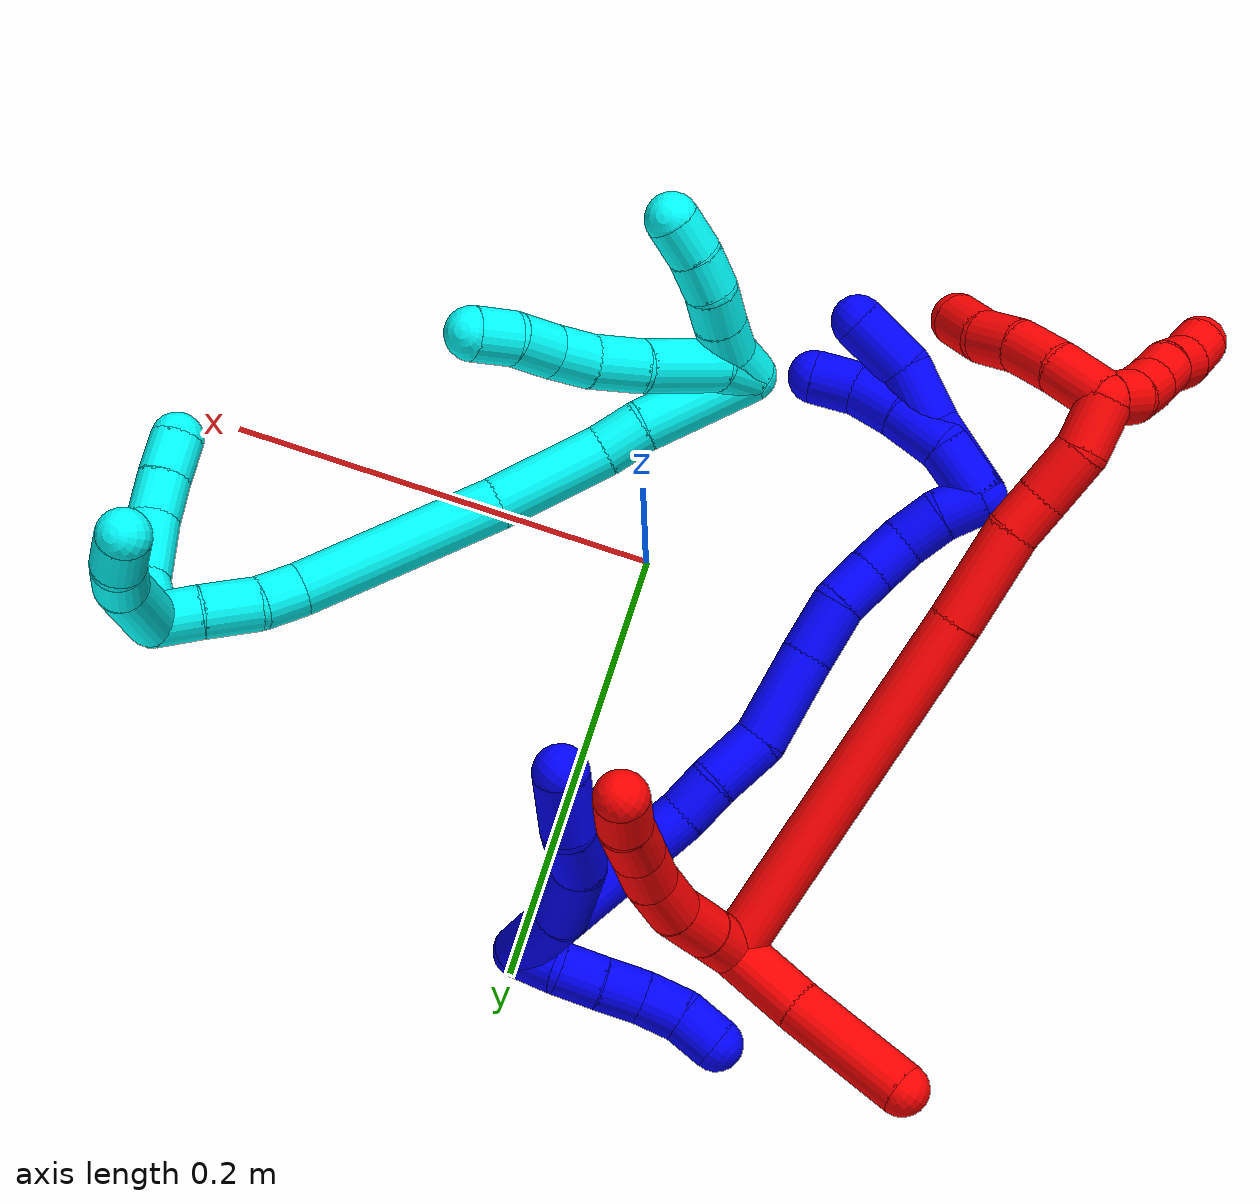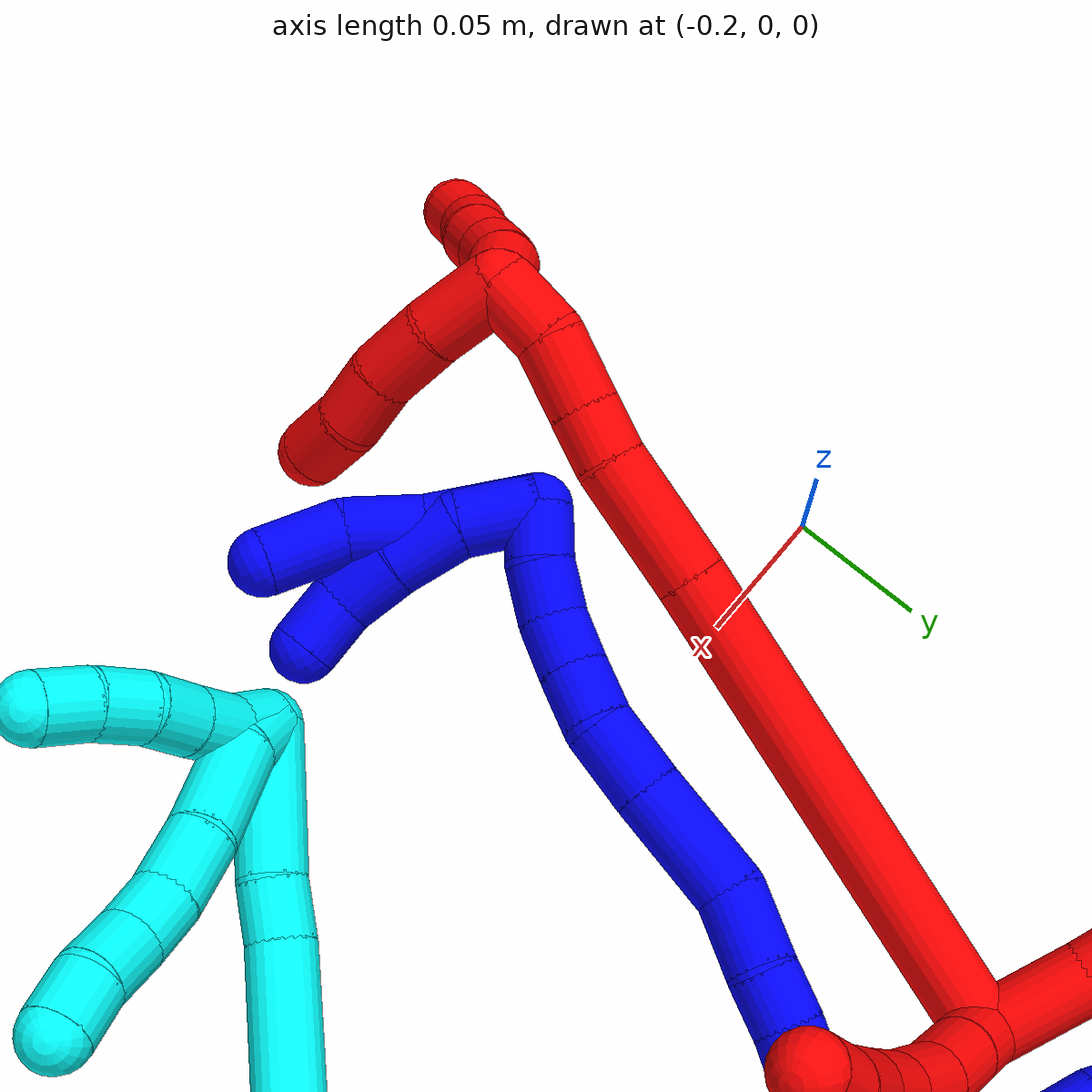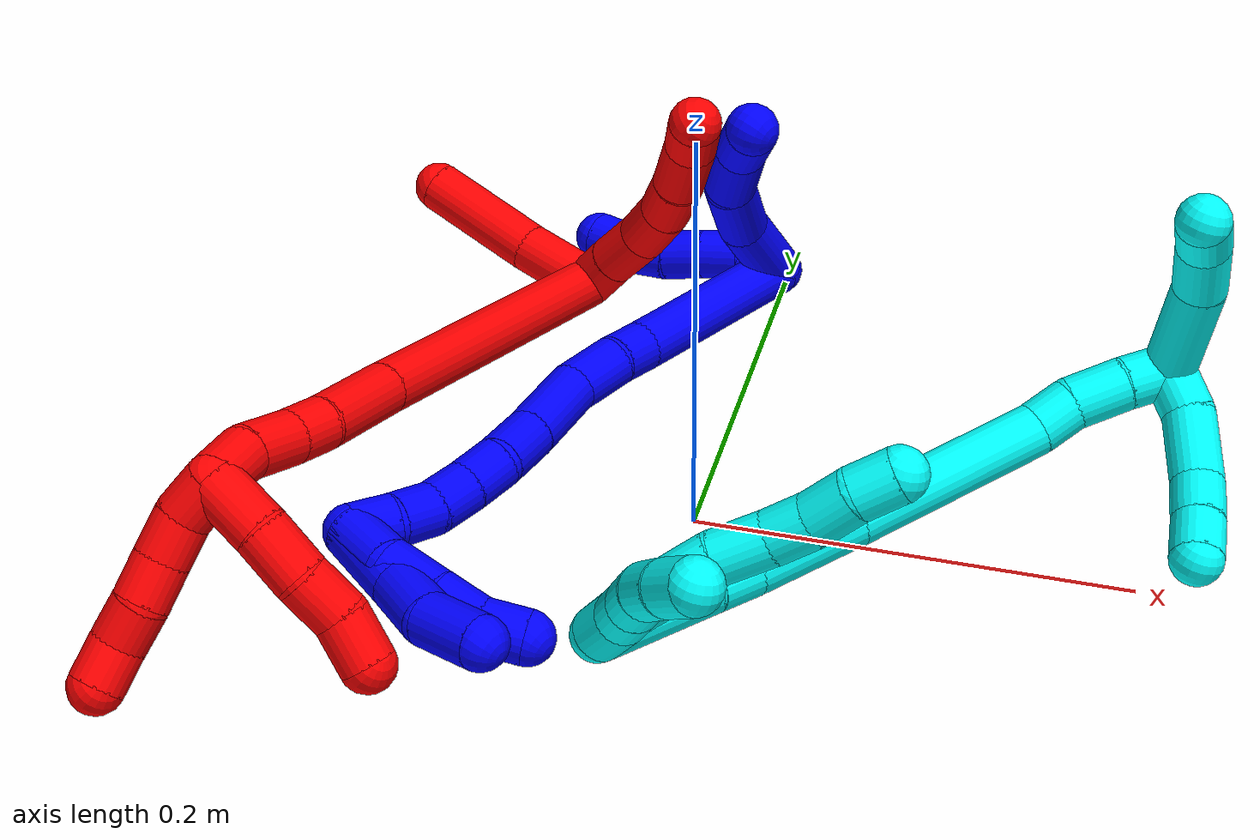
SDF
<sdf version="1.7">
 <world name="default">
  <plugin name="TubeGeneratorPlugin" filename="libtube_generator_plugin.so"/>
  <model name="photoneo_s_sensor">
   <static>1</static>
   <pose>0 0 2 1.57079 1.57079 3.14159</pose>
   <link name="link">
    <inertial><mass>0.1</mass></inertial>
    <sensor name="sensor" type="depth">
     <update_rate>30</update_rate>
     <camera>
      <horizontal_fov>1.22</horizontal_fov>
      <image><width>1920</width><height>1200</height><format>B8G8R8</format></image>
      <clip><near>0.1</near><far>4</far></clip>
      <depth_camera><output>points</output></depth_camera>
     </camera>
     <plugin name="camera_plugin" filename="libgazebo_ros_depth_camera.so">
      <baseline>0.2</baseline>
      <alwaysOn>1</alwaysOn>
      <updateRate>0.0</updateRate>
      <cameraName>camera_ir</cameraName>
      <imageTopicName>/camera/color/image_raw</imageTopicName>
      <cameraInfoTopicName>/camera/color/camera_info</cameraInfoTopicName>
      <depthImageTopicName>/camera/depth/image_raw</depthImageTopicName>
      <depthImageCameraInfoTopicName>/camera/depth/camera_info</depthImageCameraInfoTopicName>
      <pointCloudTopicName>/camera/depth/points</pointCloudTopicName>
      <frameName>fr_optical</frameName>
      <pointCloudCutoff>0.1</pointCloudCutoff>
      <pointCloudCutoffMax>2.0</pointCloudCutoffMax>
      <distortionK1>0</distortionK1>
      <distortionK2>0</distortionK2>
      <distortionK3>0</distortionK3>
      <distortionT1>0</distortionT1>
      <distortionT2>0</distortionT2>
      <CxPrime>0</CxPrime>
      <Cx>0</Cx>
      <Cy>0</Cy>
      <focalLength>0</focalLength>
      <hackBaseline>0</hackBaseline>
     </plugin>
    </sensor>
   </link>
  </model>
  <gravity>0 0 -9.8</gravity>
  <magnetic_field>6e-06 2.3e-05 -4.2e-05</magnetic_field>
  <atmosphere type="adiabatic"/>
  <physics name="default_physics" default="0" type="ode">
   <max_step_size>0.003</max_step_size>
   <real_time_factor>1</real_time_factor>
   <real_time_update_rate>1000</real_time_update_rate>
   <max_contacts>10000</max_contacts>
   <ode>
    <solver>
     <type>quick</type>
     <iters>100</iters>
     <sor>1.3</sor>
     <use_dynamic_moi_rescaling>0</use_dynamic_moi_rescaling>
    </solver>
    <constraints>
     <contact_max_correcting_vel>0</contact_max_correcting_vel>
     <contact_surface_layer>0.001</contact_surface_layer>
     <cfm>0</cfm>
     <erp>0.2</erp>
    </constraints>
   </ode>
  </physics>
  <scene><ambient>0.4 0.4 0.4 1</ambient><background>0.7 0.7 0.7 1</background><shadows>0</shadows></scene>
  <audio><device>default</device></audio>
  <spherical_coordinates>
   <surface_model>EARTH_WGS84</surface_model>
   <latitude_deg>0</latitude_deg>
   <longitude_deg>0</longitude_deg>
   <elevation>0</elevation>
   <heading_deg>0</heading_deg>
  </spherical_coordinates>
  <model name="bin">
   <static>1</static>
   <link name="bottom">
    <collision name="collision-bottom">
     <pose>0 0 -0.01 0 -0 0</pose>
     <geometry><box><size>0.8 0.6 0.02</size></box></geometry>
     <surface>
      <friction><ode><mu>100</mu><mu2>100</mu2></ode></friction>
      <contact><collide_bitmask>65535</collide_bitmask></contact>
     </surface>
    </collision>
   </link>
   <link name="west_wall">
    <collision name="collision-west_wall">
     <pose>-0.41 0 0.1 0 -0 0</pose>
     <geometry><box><size>0.02 0.6 0.2</size></box></geometry>
     <surface>
      <friction><ode><mu>100</mu><mu2>100</mu2></ode></friction>
      <contact><collide_bitmask>65535</collide_bitmask></contact>
     </surface>
    </collision>
   </link>
   <link name="east_wall">
    <collision name="collision-east_wall">
     <pose>0.41 0 0.1 0 -0 0</pose>
     <geometry><box><size>0.02 0.6 0.2</size></box></geometry>
     <surface>
      <friction><ode><mu>100</mu><mu2>100</mu2></ode></friction>
      <contact><collide_bitmask>65535</collide_bitmask></contact>
     </surface>
    </collision>
   </link>
   <link name="south_wall">
    <collision name="collision-south_wall">
     <pose>0 -0.31 0.1 0 -0 0</pose>
     <geometry><box><size>0.8 0.02 0.2</size></box></geometry>
     <surface>
      <friction><ode><mu>100</mu><mu2>100</mu2></ode></friction>
      <contact><collide_bitmask>65535</collide_bitmask></contact>
     </surface>
    </collision>
   </link>
   <link name="north_wall">
    <collision name="collision-north_wall">
     <pose>0 0.31 0.1 0 -0 0</pose>
     <geometry><box><size>0.8 0.02 0.2</size></box></geometry>
     <surface>
      <friction><ode><mu>100</mu><mu2>100</mu2></ode></friction>
      <contact><collide_bitmask>65535</collide_bitmask></contact>
     </surface>
    </collision>
   </link>
  </model>
  <model name="1">
   <static>0</static>
   <link name="1">
    <collision name="collision-cylinder-e_1_2_8">
     <pose>0.015552 -0.01507 0.005768 1.20526 0.766965 0.541527</pose>
     <geometry><cylinder><radius>0.0125</radius><length>0.044822</length></cylinder></geometry>
     <surface>
      <friction><ode><mu>1.16</mu><mu2>1.16</mu2><slip1>0</slip1><slip2>0</slip2></ode></friction>
      <contact><ode><kp>1e+06</kp><kd>1</kd><max_vel>0</max_vel><min_depth>0.001</min_depth></ode></contact>
     </surface>
    </collision>
    <visual name="visual-cylinder-e_1_2_8">
     <pose>0.015552 -0.01507 0.005768 1.20526 0.766965 0.541527</pose>
     <geometry><cylinder><radius>0.0125</radius><length>0.044822</length></cylinder></geometry>
     <material><ambient>0 0 1 1</ambient></material>
    </visual>
    <collision name="collision-cylinder-e_2_8_9">
     <pose>0.046693 -0.043123 0.011429 1.57901 0.876353 0.882682</pose>
     <geometry><cylinder><radius>0.0125</radius><length>0.040575</length></cylinder></geometry>
     <surface>
      <friction><ode><mu>1.16</mu><mu2>1.16</mu2><slip1>0</slip1><slip2>0</slip2></ode></friction>
      <contact><ode><kp>1e+06</kp><kd>1</kd><max_vel>0</max_vel><min_depth>0.001</min_depth></ode></contact>
     </surface>
    </collision>
    <visual name="visual-cylinder-e_2_8_9">
     <pose>0.046693 -0.043123 0.011429 1.57901 0.876353 0.882682</pose>
     <geometry><cylinder><radius>0.0125</radius><length>0.040575</length></cylinder></geometry>
     <material><ambient>0 0 1 1</ambient></material>
    </visual>
    <collision name="collision-cylinder-e_3_9_10">
     <pose>0.076599 -0.062643 0.007903 2.05277 1.09499 1.57774</pose>
     <geometry><cylinder><radius>0.0125</radius><length>0.032211</length></cylinder></geometry>
     <surface>
      <friction><ode><mu>1.16</mu><mu2>1.16</mu2><slip1>0</slip1><slip2>0</slip2></ode></friction>
      <contact><ode><kp>1e+06</kp><kd>1</kd><max_vel>0</max_vel><min_depth>0.001</min_depth></ode></contact>
     </surface>
    </collision>
    <visual name="visual-cylinder-e_3_9_10">
     <pose>0.076599 -0.062643 0.007903 2.05277 1.09499 1.57774</pose>
     <geometry><cylinder><radius>0.0125</radius><length>0.032211</length></cylinder></geometry>
     <material><ambient>0 0 1 1</ambient></material>
    </visual>
    <collision name="collision-cylinder-e_4_10_6">
     <pose>0.102608 -0.07858 -0.001619 2.14662 0.806566 1.33192</pose>
     <geometry><cylinder><radius>0.0125</radius><length>0.032391</length></cylinder></geometry>
     <surface>
      <friction><ode><mu>1.16</mu><mu2>1.16</mu2><slip1>0</slip1><slip2>0</slip2></ode></friction>
      <contact><ode><kp>1e+06</kp><kd>1</kd><max_vel>0</max_vel><min_depth>0.001</min_depth></ode></contact>
     </surface>
    </collision>
    <visual name="visual-cylinder-e_4_10_6">
     <pose>0.102608 -0.07858 -0.001619 2.14662 0.806566 1.33192</pose>
     <geometry><cylinder><radius>0.0125</radius><length>0.032391</length></cylinder></geometry>
     <material><ambient>0 0 1 1</ambient></material>
    </visual>
    <collision name="collision-cylinder-e_1_2_11">
     <pose>-0.0002 -0.00325 0.009455 0.33112 -0.019964 -0.003336</pose>
     <geometry><cylinder><radius>0.0125</radius><length>0.02</length></cylinder></geometry>
     <surface>
      <friction><ode><mu>1.16</mu><mu2>1.16</mu2><slip1>0</slip1><slip2>0</slip2></ode></friction>
      <contact><ode><kp>1e+06</kp><kd>1</kd><max_vel>0</max_vel><min_depth>0.001</min_depth></ode></contact>
     </surface>
    </collision>
    <visual name="visual-cylinder-e_1_2_11">
     <pose>-0.0002 -0.00325 0.009455 0.33112 -0.019964 -0.003336</pose>
     <geometry><cylinder><radius>0.0125</radius><length>0.02</length></cylinder></geometry>
     <material><ambient>0 0 1 1</ambient></material>
    </visual>
    <collision name="collision-cylinder-e_2_11_12">
     <pose>-0.003932 -0.009812 0.027659 0.361795 -0.361041 -0.066735</pose>
     <geometry><cylinder><radius>0.0125</radius><length>0.02</length></cylinder></geometry>
     <surface>
      <friction><ode><mu>1.16</mu><mu2>1.16</mu2><slip1>0</slip1><slip2>0</slip2></ode></friction>
      <contact><ode><kp>1e+06</kp><kd>1</kd><max_vel>0</max_vel><min_depth>0.001</min_depth></ode></contact>
     </surface>
    </collision>
    <visual name="visual-cylinder-e_2_11_12">
     <pose>-0.003932 -0.009812 0.027659 0.361795 -0.361041 -0.066735</pose>
     <geometry><cylinder><radius>0.0125</radius><length>0.02</length></cylinder></geometry>
     <material><ambient>0 0 1 1</ambient></material>
    </visual>
    <collision name="collision-cylinder-e_3_12_13">
     <pose>-0.011643 -0.01649 0.044848 0.379571 -0.431103 -0.084071</pose>
     <geometry><cylinder><radius>0.0125</radius><length>0.02</length></cylinder></geometry>
     <surface>
      <friction><ode><mu>1.16</mu><mu2>1.16</mu2><slip1>0</slip1><slip2>0</slip2></ode></friction>
      <contact><ode><kp>1e+06</kp><kd>1</kd><max_vel>0</max_vel><min_depth>0.001</min_depth></ode></contact>
     </surface>
    </collision>
    <visual name="visual-cylinder-e_3_12_13">
     <pose>-0.011643 -0.01649 0.044848 0.379571 -0.431103 -0.084071</pose>
     <geometry><cylinder><radius>0.0125</radius><length>0.02</length></cylinder></geometry>
     <material><ambient>0 0 1 1</ambient></material>
    </visual>
    <collision name="collision-cylinder-e_4_13_14">
     <pose>-0.018433 -0.022549 0.062556 0.282725 -0.264153 -0.037808</pose>
     <geometry><cylinder><radius>0.0125</radius><length>0.02</length></cylinder></geometry>
     <surface>
      <friction><ode><mu>1.16</mu><mu2>1.16</mu2><slip1>0</slip1><slip2>0</slip2></ode></friction>
      <contact><ode><kp>1e+06</kp><kd>1</kd><max_vel>0</max_vel><min_depth>0.001</min_depth></ode></contact>
     </surface>
    </collision>
    <visual name="visual-cylinder-e_4_13_14">
     <pose>-0.018433 -0.022549 0.062556 0.282725 -0.264153 -0.037808</pose>
     <geometry><cylinder><radius>0.0125</radius><length>0.02</length></cylinder></geometry>
     <material><ambient>0 0 1 1</ambient></material>
    </visual>
    <collision name="collision-cylinder-e_5_14_5">
     <pose>-0.022983 -0.025423 0.081634 0.018498 -0.195157 -0.001811</pose>
     <geometry><cylinder><radius>0.0125</radius><length>0.02</length></cylinder></geometry>
     <surface>
      <friction><ode><mu>1.16</mu><mu2>1.16</mu2><slip1>0</slip1><slip2>0</slip2></ode></friction>
      <contact><ode><kp>1e+06</kp><kd>1</kd><max_vel>0</max_vel><min_depth>0.001</min_depth></ode></contact>
     </surface>
    </collision>
    <visual name="visual-cylinder-e_5_14_5">
     <pose>-0.022983 -0.025423 0.081634 0.018498 -0.195157 -0.001811</pose>
     <geometry><cylinder><radius>0.0125</radius><length>0.02</length></cylinder></geometry>
     <material><ambient>0 0 1 1</ambient></material>
    </visual>
    <collision name="collision-cylinder-e_1_2_15">
     <pose>-0.00971 -0.046748 0.005848 1.44634 -0.203254 -0.179548</pose>
     <geometry><cylinder><radius>0.0125</radius><length>0.096205</length></cylinder></geometry>
     <surface>
      <friction><ode><mu>1.16</mu><mu2>1.16</mu2><slip1>0</slip1><slip2>0</slip2></ode></friction>
      <contact><ode><kp>1e+06</kp><kd>1</kd><max_vel>0</max_vel><min_depth>0.001</min_depth></ode></contact>
     </surface>
    </collision>
    <visual name="visual-cylinder-e_1_2_15">
     <pose>-0.00971 -0.046748 0.005848 1.44634 -0.203254 -0.179548</pose>
     <geometry><cylinder><radius>0.0125</radius><length>0.096205</length></cylinder></geometry>
     <material><ambient>0 0 1 1</ambient></material>
    </visual>
    <collision name="collision-cylinder-e_2_15_16">
     <pose>-0.019908 -0.103772 0.012069 1.53448 -0.047486 -0.045793</pose>
     <geometry><cylinder><radius>0.0125</radius><length>0.020589</length></cylinder></geometry>
     <surface>
      <friction><ode><mu>1.16</mu><mu2>1.16</mu2><slip1>0</slip1><slip2>0</slip2></ode></friction>
      <contact><ode><kp>1e+06</kp><kd>1</kd><max_vel>0</max_vel><min_depth>0.001</min_depth></ode></contact>
     </surface>
    </collision>
    <visual name="visual-cylinder-e_2_15_16">
     <pose>-0.019908 -0.103772 0.012069 1.53448 -0.047486 -0.045793</pose>
     <geometry><cylinder><radius>0.0125</radius><length>0.020589</length></cylinder></geometry>
     <material><ambient>0 0 1 1</ambient></material>
    </visual>
    <collision name="collision-cylinder-e_3_16_17">
     <pose>-0.02378 -0.127712 0.013582 1.48764 -0.241914 -0.222756</pose>
     <geometry><cylinder><radius>0.0125</radius><length>0.028245</length></cylinder></geometry>
     <surface>
      <friction><ode><mu>1.16</mu><mu2>1.16</mu2><slip1>0</slip1><slip2>0</slip2></ode></friction>
      <contact><ode><kp>1e+06</kp><kd>1</kd><max_vel>0</max_vel><min_depth>0.001</min_depth></ode></contact>
     </surface>
    </collision>
    <visual name="visual-cylinder-e_3_16_17">
     <pose>-0.02378 -0.127712 0.013582 1.48764 -0.241914 -0.222756</pose>
     <geometry><cylinder><radius>0.0125</radius><length>0.028245</length></cylinder></geometry>
     <material><ambient>0 0 1 1</ambient></material>
    </visual>
    <collision name="collision-cylinder-e_4_17_18">
     <pose>-0.028704 -0.163038 0.00989 1.79019 -0.069323 -0.086464</pose>
     <geometry><cylinder><radius>0.0125</radius><length>0.044495</length></cylinder></geometry>
     <surface>
      <friction><ode><mu>1.16</mu><mu2>1.16</mu2><slip1>0</slip1><slip2>0</slip2></ode></friction>
      <contact><ode><kp>1e+06</kp><kd>1</kd><max_vel>0</max_vel><min_depth>0.001</min_depth></ode></contact>
     </surface>
    </collision>
    <visual name="visual-cylinder-e_4_17_18">
     <pose>-0.028704 -0.163038 0.00989 1.79019 -0.069323 -0.086464</pose>
     <geometry><cylinder><radius>0.0125</radius><length>0.044495</length></cylinder></geometry>
     <material><ambient>0 0 1 1</ambient></material>
    </visual>
    <collision name="collision-cylinder-e_5_18_19">
     <pose>-0.03063 -0.198487 0.002619 1.74602 -0.02747 -0.032759</pose>
     <geometry><cylinder><radius>0.0125</radius><length>0.028012</length></cylinder></geometry>
     <surface>
      <friction><ode><mu>1.16</mu><mu2>1.16</mu2><slip1>0</slip1><slip2>0</slip2></ode></friction>
      <contact><ode><kp>1e+06</kp><kd>1</kd><max_vel>0</max_vel><min_depth>0.001</min_depth></ode></contact>
     </surface>
    </collision>
    <visual name="visual-cylinder-e_5_18_19">
     <pose>-0.03063 -0.198487 0.002619 1.74602 -0.02747 -0.032759</pose>
     <geometry><cylinder><radius>0.0125</radius><length>0.028012</length></cylinder></geometry>
     <material><ambient>0 0 1 1</ambient></material>
    </visual>
    <collision name="collision-cylinder-e_6_19_20">
     <pose>-0.033699 -0.222435 0.000482 1.54093 -0.258146 -0.250628</pose>
     <geometry><cylinder><radius>0.0125</radius><length>0.021029</length></cylinder></geometry>
     <surface>
      <friction><ode><mu>1.16</mu><mu2>1.16</mu2><slip1>0</slip1><slip2>0</slip2></ode></friction>
      <contact><ode><kp>1e+06</kp><kd>1</kd><max_vel>0</max_vel><min_depth>0.001</min_depth></ode></contact>
     </surface>
    </collision>
    <visual name="visual-cylinder-e_6_19_20">
     <pose>-0.033699 -0.222435 0.000482 1.54093 -0.258146 -0.250628</pose>
     <geometry><cylinder><radius>0.0125</radius><length>0.021029</length></cylinder></geometry>
     <material><ambient>0 0 1 1</ambient></material>
    </visual>
    <collision name="collision-cylinder-e_7_20_21">
     <pose>-0.038544 -0.242534 0.001491 1.49991 -0.213598 -0.19907</pose>
     <geometry><cylinder><radius>0.0125</radius><length>0.020388</length></cylinder></geometry>
     <surface>
      <friction><ode><mu>1.16</mu><mu2>1.16</mu2><slip1>0</slip1><slip2>0</slip2></ode></friction>
      <contact><ode><kp>1e+06</kp><kd>1</kd><max_vel>0</max_vel><min_depth>0.001</min_depth></ode></contact>
     </surface>
    </collision>
    <visual name="visual-cylinder-e_7_20_21">
     <pose>-0.038544 -0.242534 0.001491 1.49991 -0.213598 -0.19907</pose>
     <geometry><cylinder><radius>0.0125</radius><length>0.020388</length></cylinder></geometry>
     <material><ambient>0 0 1 1</ambient></material>
    </visual>
    <collision name="collision-cylinder-e_8_21_22">
     <pose>-0.041041 -0.262587 0.004623 1.33539 -0.032249 -0.025429</pose>
     <geometry><cylinder><radius>0.0125</radius><length>0.020817</length></cylinder></geometry>
     <surface>
      <friction><ode><mu>1.16</mu><mu2>1.16</mu2><slip1>0</slip1><slip2>0</slip2></ode></friction>
      <contact><ode><kp>1e+06</kp><kd>1</kd><max_vel>0</max_vel><min_depth>0.001</min_depth></ode></contact>
     </surface>
    </collision>
    <visual name="visual-cylinder-e_8_21_22">
     <pose>-0.041041 -0.262587 0.004623 1.33539 -0.032249 -0.025429</pose>
     <geometry><cylinder><radius>0.0125</radius><length>0.020817</length></cylinder></geometry>
     <material><ambient>0 0 1 1</ambient></material>
    </visual>
    <collision name="collision-cylinder-e_9_22_1">
     <pose>-0.042948 -0.281783 0.011208 1.14136 -0.156065 -0.100302</pose>
     <geometry><cylinder><radius>0.0125</radius><length>0.020219</length></cylinder></geometry>
     <surface>
      <friction><ode><mu>1.16</mu><mu2>1.16</mu2><slip1>0</slip1><slip2>0</slip2></ode></friction>
      <contact><ode><kp>1e+06</kp><kd>1</kd><max_vel>0</max_vel><min_depth>0.001</min_depth></ode></contact>
     </surface>
    </collision>
    <visual name="visual-cylinder-e_9_22_1">
     <pose>-0.042948 -0.281783 0.011208 1.14136 -0.156065 -0.100302</pose>
     <geometry><cylinder><radius>0.0125</radius><length>0.020219</length></cylinder></geometry>
     <material><ambient>0 0 1 1</ambient></material>
    </visual>
    <collision name="collision-cylinder-e_1_1_23">
     <pose>-0.043276 -0.296441 -0.003961 2.86064 0.061708 0.429783</pose>
     <geometry><cylinder><radius>0.0125</radius><length>0.040308</length></cylinder></geometry>
     <surface>
      <friction><ode><mu>1.16</mu><mu2>1.16</mu2><slip1>0</slip1><slip2>0</slip2></ode></friction>
      <contact><ode><kp>1e+06</kp><kd>1</kd><max_vel>0</max_vel><min_depth>0.001</min_depth></ode></contact>
     </surface>
    </collision>
    <visual name="visual-cylinder-e_1_1_23">
     <pose>-0.043276 -0.296441 -0.003961 2.86064 0.061708 0.429783</pose>
     <geometry><cylinder><radius>0.0125</radius><length>0.040308</length></cylinder></geometry>
     <material><ambient>0 0 1 1</ambient></material>
    </visual>
    <collision name="collision-cylinder-e_2_23_24">
     <pose>-0.039024 -0.307888 -0.036407 2.72087 0.206409 0.903259</pose>
     <geometry><cylinder><radius>0.0125</radius><length>0.029368</length></cylinder></geometry>
     <surface>
      <friction><ode><mu>1.16</mu><mu2>1.16</mu2><slip1>0</slip1><slip2>0</slip2></ode></friction>
      <contact><ode><kp>1e+06</kp><kd>1</kd><max_vel>0</max_vel><min_depth>0.001</min_depth></ode></contact>
     </surface>
    </collision>
    <visual name="visual-cylinder-e_2_23_24">
     <pose>-0.039024 -0.307888 -0.036407 2.72087 0.206409 0.903259</pose>
     <geometry><cylinder><radius>0.0125</radius><length>0.029368</length></cylinder></geometry>
     <material><ambient>0 0 1 1</ambient></material>
    </visual>
    <collision name="collision-cylinder-e_3_24_4">
     <pose>-0.031352 -0.314887 -0.063909 3.06329 0.312576 2.65428</pose>
     <geometry><cylinder><radius>0.0125</radius><length>0.030324</length></cylinder></geometry>
     <surface>
      <friction><ode><mu>1.16</mu><mu2>1.16</mu2><slip1>0</slip1><slip2>0</slip2></ode></friction>
      <contact><ode><kp>1e+06</kp><kd>1</kd><max_vel>0</max_vel><min_depth>0.001</min_depth></ode></contact>
     </surface>
    </collision>
    <visual name="visual-cylinder-e_3_24_4">
     <pose>-0.031352 -0.314887 -0.063909 3.06329 0.312576 2.65428</pose>
     <geometry><cylinder><radius>0.0125</radius><length>0.030324</length></cylinder></geometry>
     <material><ambient>0 0 1 1</ambient></material>
    </visual>
    <collision name="collision-cylinder-e_1_1_25">
     <pose>-0.042289 -0.29449 0.001358 2.88827 0.152894 1.08305</pose>
     <geometry><cylinder><radius>0.0125</radius><length>0.029281</length></cylinder></geometry>
     <surface>
      <friction><ode><mu>1.16</mu><mu2>1.16</mu2><slip1>0</slip1><slip2>0</slip2></ode></friction>
      <contact><ode><kp>1e+06</kp><kd>1</kd><max_vel>0</max_vel><min_depth>0.001</min_depth></ode></contact>
     </surface>
    </collision>
    <visual name="visual-cylinder-e_1_1_25">
     <pose>-0.042289 -0.29449 0.001358 2.88827 0.152894 1.08305</pose>
     <geometry><cylinder><radius>0.0125</radius><length>0.029281</length></cylinder></geometry>
     <material><ambient>0 0 1 1</ambient></material>
    </visual>
    <collision name="collision-cylinder-e_2_25_26">
     <pose>-0.039967 -0.297299 -0.02596 -3.08023 0.006967 -0.226041</pose>
     <geometry><cylinder><radius>0.0125</radius><length>0.026671</length></cylinder></geometry>
     <surface>
      <friction><ode><mu>1.16</mu><mu2>1.16</mu2><slip1>0</slip1><slip2>0</slip2></ode></friction>
      <contact><ode><kp>1e+06</kp><kd>1</kd><max_vel>0</max_vel><min_depth>0.001</min_depth></ode></contact>
     </surface>
    </collision>
    <visual name="visual-cylinder-e_2_25_26">
     <pose>-0.039967 -0.297299 -0.02596 -3.08023 0.006967 -0.226041</pose>
     <geometry><cylinder><radius>0.0125</radius><length>0.026671</length></cylinder></geometry>
     <material><ambient>0 0 1 1</ambient></material>
    </visual>
    <collision name="collision-cylinder-e_3_26_27">
     <pose>-0.040792 -0.294663 -0.050463 -2.98059 -0.080791 0.928853</pose>
     <geometry><cylinder><radius>0.0125</radius><length>0.022753</length></cylinder></geometry>
     <surface>
      <friction><ode><mu>1.16</mu><mu2>1.16</mu2><slip1>0</slip1><slip2>0</slip2></ode></friction>
      <contact><ode><kp>1e+06</kp><kd>1</kd><max_vel>0</max_vel><min_depth>0.001</min_depth></ode></contact>
     </surface>
    </collision>
    <visual name="visual-cylinder-e_3_26_27">
     <pose>-0.040792 -0.294663 -0.050463 -2.98059 -0.080791 0.928853</pose>
     <geometry><cylinder><radius>0.0125</radius><length>0.022753</length></cylinder></geometry>
     <material><ambient>0 0 1 1</ambient></material>
    </visual>
    <collision name="collision-cylinder-e_4_27_3">
     <pose>-0.040611 -0.288402 -0.071269 -2.70866 0.103349 -0.461987</pose>
     <geometry><cylinder><radius>0.0125</radius><length>0.021295</length></cylinder></geometry>
     <surface>
      <friction><ode><mu>1.16</mu><mu2>1.16</mu2><slip1>0</slip1><slip2>0</slip2></ode></friction>
      <contact><ode><kp>1e+06</kp><kd>1</kd><max_vel>0</max_vel><min_depth>0.001</min_depth></ode></contact>
     </surface>
    </collision>
    <visual name="visual-cylinder-e_4_27_3">
     <pose>-0.040611 -0.288402 -0.071269 -2.70866 0.103349 -0.461987</pose>
     <geometry><cylinder><radius>0.0125</radius><length>0.021295</length></cylinder></geometry>
     <material><ambient>0 0 1 1</ambient></material>
    </visual>
    <collision name="collision-sphere-3">
     <pose>-0.039513 -0.283959 -0.080883 0 -0 0</pose>
     <geometry><sphere><radius>0.0125</radius></sphere></geometry>
     <surface>
      <friction><ode><mu>1.16</mu><mu2>1.16</mu2><slip1>0</slip1><slip2>0</slip2></ode></friction>
      <contact><ode><kp>1e+06</kp><kd>1</kd><max_vel>0</max_vel><min_depth>0.001</min_depth></ode></contact>
     </surface>
    </collision>
    <visual name="visual-sphere-3">
     <pose>-0.039513 -0.283959 -0.080883 0 -0 0</pose>
     <geometry><sphere><radius>0.0125</radius></sphere></geometry>
     <material><ambient>0 0 1 1</ambient></material>
    </visual>
    <collision name="collision-sphere-27">
     <pose>-0.04171 -0.292845 -0.061656 0 -0 0</pose>
     <geometry><sphere><radius>0.0125</radius></sphere></geometry>
     <surface>
      <friction><ode><mu>1.16</mu><mu2>1.16</mu2><slip1>0</slip1><slip2>0</slip2></ode></friction>
      <contact><ode><kp>1e+06</kp><kd>1</kd><max_vel>0</max_vel><min_depth>0.001</min_depth></ode></contact>
     </surface>
    </collision>
    <visual name="visual-sphere-27">
     <pose>-0.04171 -0.292845 -0.061656 0 -0 0</pose>
     <geometry><sphere><radius>0.0125</radius></sphere></geometry>
     <material><ambient>0 0 1 1</ambient></material>
    </visual>
    <collision name="collision-sphere-26">
     <pose>-0.039874 -0.296481 -0.03927 0 -0 0</pose>
     <geometry><sphere><radius>0.0125</radius></sphere></geometry>
     <surface>
      <friction><ode><mu>1.16</mu><mu2>1.16</mu2><slip1>0</slip1><slip2>0</slip2></ode></friction>
      <contact><ode><kp>1e+06</kp><kd>1</kd><max_vel>0</max_vel><min_depth>0.001</min_depth></ode></contact>
     </surface>
    </collision>
    <visual name="visual-sphere-26">
     <pose>-0.039874 -0.296481 -0.03927 0 -0 0</pose>
     <geometry><sphere><radius>0.0125</radius></sphere></geometry>
     <material><ambient>0 0 1 1</ambient></material>
    </visual>
    <collision name="collision-sphere-25">
     <pose>-0.040059 -0.298116 -0.01265 0 -0 0</pose>
     <geometry><sphere><radius>0.0125</radius></sphere></geometry>
     <surface>
      <friction><ode><mu>1.16</mu><mu2>1.16</mu2><slip1>0</slip1><slip2>0</slip2></ode></friction>
      <contact><ode><kp>1e+06</kp><kd>1</kd><max_vel>0</max_vel><min_depth>0.001</min_depth></ode></contact>
     </surface>
    </collision>
    <visual name="visual-sphere-25">
     <pose>-0.040059 -0.298116 -0.01265 0 -0 0</pose>
     <geometry><sphere><radius>0.0125</radius></sphere></geometry>
     <material><ambient>0 0 1 1</ambient></material>
    </visual>
    <collision name="collision-sphere-4">
     <pose>-0.026689 -0.316015 -0.078292 0 -0 0</pose>
     <geometry><sphere><radius>0.0125</radius></sphere></geometry>
     <surface>
      <friction><ode><mu>1.16</mu><mu2>1.16</mu2><slip1>0</slip1><slip2>0</slip2></ode></friction>
      <contact><ode><kp>1e+06</kp><kd>1</kd><max_vel>0</max_vel><min_depth>0.001</min_depth></ode></contact>
     </surface>
    </collision>
    <visual name="visual-sphere-4">
     <pose>-0.026689 -0.316015 -0.078292 0 -0 0</pose>
     <geometry><sphere><radius>0.0125</radius></sphere></geometry>
     <material><ambient>0 0 1 1</ambient></material>
    </visual>
    <collision name="collision-sphere-24">
     <pose>-0.036015 -0.313758 -0.049525 0 -0 0</pose>
     <geometry><sphere><radius>0.0125</radius></sphere></geometry>
     <surface>
      <friction><ode><mu>1.16</mu><mu2>1.16</mu2><slip1>0</slip1><slip2>0</slip2></ode></friction>
      <contact><ode><kp>1e+06</kp><kd>1</kd><max_vel>0</max_vel><min_depth>0.001</min_depth></ode></contact>
     </surface>
    </collision>
    <visual name="visual-sphere-24">
     <pose>-0.036015 -0.313758 -0.049525 0 -0 0</pose>
     <geometry><sphere><radius>0.0125</radius></sphere></geometry>
     <material><ambient>0 0 1 1</ambient></material>
    </visual>
    <collision name="collision-sphere-23">
     <pose>-0.042033 -0.302018 -0.023288 0 -0 0</pose>
     <geometry><sphere><radius>0.0125</radius></sphere></geometry>
     <surface>
      <friction><ode><mu>1.16</mu><mu2>1.16</mu2><slip1>0</slip1><slip2>0</slip2></ode></friction>
      <contact><ode><kp>1e+06</kp><kd>1</kd><max_vel>0</max_vel><min_depth>0.001</min_depth></ode></contact>
     </surface>
    </collision>
    <visual name="visual-sphere-23">
     <pose>-0.042033 -0.302018 -0.023288 0 -0 0</pose>
     <geometry><sphere><radius>0.0125</radius></sphere></geometry>
     <material><ambient>0 0 1 1</ambient></material>
    </visual>
    <collision name="collision-sphere-1">
     <pose>-0.044519 -0.290863 0.015366 0 -0 0</pose>
     <geometry><sphere><radius>0.0125</radius></sphere></geometry>
     <surface>
      <friction><ode><mu>1.16</mu><mu2>1.16</mu2><slip1>0</slip1><slip2>0</slip2></ode></friction>
      <contact><ode><kp>1e+06</kp><kd>1</kd><max_vel>0</max_vel><min_depth>0.001</min_depth></ode></contact>
     </surface>
    </collision>
    <visual name="visual-sphere-1">
     <pose>-0.044519 -0.290863 0.015366 0 -0 0</pose>
     <geometry><sphere><radius>0.0125</radius></sphere></geometry>
     <material><ambient>0 0 1 1</ambient></material>
    </visual>
    <collision name="collision-sphere-22">
     <pose>-0.041376 -0.272703 0.00705 0 -0 0</pose>
     <geometry><sphere><radius>0.0125</radius></sphere></geometry>
     <surface>
      <friction><ode><mu>1.16</mu><mu2>1.16</mu2><slip1>0</slip1><slip2>0</slip2></ode></friction>
      <contact><ode><kp>1e+06</kp><kd>1</kd><max_vel>0</max_vel><min_depth>0.001</min_depth></ode></contact>
     </surface>
    </collision>
    <visual name="visual-sphere-22">
     <pose>-0.041376 -0.272703 0.00705 0 -0 0</pose>
     <geometry><sphere><radius>0.0125</radius></sphere></geometry>
     <material><ambient>0 0 1 1</ambient></material>
    </visual>
    <collision name="collision-sphere-21">
     <pose>-0.040705 -0.252471 0.002197 0 -0 0</pose>
     <geometry><sphere><radius>0.0125</radius></sphere></geometry>
     <surface>
      <friction><ode><mu>1.16</mu><mu2>1.16</mu2><slip1>0</slip1><slip2>0</slip2></ode></friction>
      <contact><ode><kp>1e+06</kp><kd>1</kd><max_vel>0</max_vel><min_depth>0.001</min_depth></ode></contact>
     </surface>
    </collision>
    <visual name="visual-sphere-21">
     <pose>-0.040705 -0.252471 0.002197 0 -0 0</pose>
     <geometry><sphere><radius>0.0125</radius></sphere></geometry>
     <material><ambient>0 0 1 1</ambient></material>
    </visual>
    <collision name="collision-sphere-11">
     <pose>-0.000399 -0.006501 0.01891 0 -0 0</pose>
     <geometry><sphere><radius>0.0125</radius></sphere></geometry>
     <surface>
      <friction><ode><mu>1.16</mu><mu2>1.16</mu2><slip1>0</slip1><slip2>0</slip2></ode></friction>
      <contact><ode><kp>1e+06</kp><kd>1</kd><max_vel>0</max_vel><min_depth>0.001</min_depth></ode></contact>
     </surface>
    </collision>
    <visual name="visual-sphere-11">
     <pose>-0.000399 -0.006501 0.01891 0 -0 0</pose>
     <geometry><sphere><radius>0.0125</radius></sphere></geometry>
     <material><ambient>0 0 1 1</ambient></material>
    </visual>
    <collision name="collision-sphere-6">
     <pose>0.1143 -0.08798 -0.007722 0 -0 0</pose>
     <geometry><sphere><radius>0.0125</radius></sphere></geometry>
     <surface>
      <friction><ode><mu>1.16</mu><mu2>1.16</mu2><slip1>0</slip1><slip2>0</slip2></ode></friction>
      <contact><ode><kp>1e+06</kp><kd>1</kd><max_vel>0</max_vel><min_depth>0.001</min_depth></ode></contact>
     </surface>
    </collision>
    <visual name="visual-sphere-6">
     <pose>0.1143 -0.08798 -0.007722 0 -0 0</pose>
     <geometry><sphere><radius>0.0125</radius></sphere></geometry>
     <material><ambient>0 0 1 1</ambient></material>
    </visual>
    <collision name="collision-sphere-10">
     <pose>0.090916 -0.06918 0.004483 0 -0 0</pose>
     <geometry><sphere><radius>0.0125</radius></sphere></geometry>
     <surface>
      <friction><ode><mu>1.16</mu><mu2>1.16</mu2><slip1>0</slip1><slip2>0</slip2></ode></friction>
      <contact><ode><kp>1e+06</kp><kd>1</kd><max_vel>0</max_vel><min_depth>0.001</min_depth></ode></contact>
     </surface>
    </collision>
    <visual name="visual-sphere-10">
     <pose>0.090916 -0.06918 0.004483 0 -0 0</pose>
     <geometry><sphere><radius>0.0125</radius></sphere></geometry>
     <material><ambient>0 0 1 1</ambient></material>
    </visual>
    <collision name="collision-sphere-9">
     <pose>0.062283 -0.056106 0.011322 0 -0 0</pose>
     <geometry><sphere><radius>0.0125</radius></sphere></geometry>
     <surface>
      <friction><ode><mu>1.16</mu><mu2>1.16</mu2><slip1>0</slip1><slip2>0</slip2></ode></friction>
      <contact><ode><kp>1e+06</kp><kd>1</kd><max_vel>0</max_vel><min_depth>0.001</min_depth></ode></contact>
     </surface>
    </collision>
    <visual name="visual-sphere-9">
     <pose>0.062283 -0.056106 0.011322 0 -0 0</pose>
     <geometry><sphere><radius>0.0125</radius></sphere></geometry>
     <material><ambient>0 0 1 1</ambient></material>
    </visual>
    <collision name="collision-sphere-2">
     <geometry><sphere><radius>0.0125</radius></sphere></geometry>
     <surface>
      <friction><ode><mu>1.16</mu><mu2>1.16</mu2><slip1>0</slip1><slip2>0</slip2></ode></friction>
      <contact><ode><kp>1e+06</kp><kd>1</kd><max_vel>0</max_vel><min_depth>0.001</min_depth></ode></contact>
     </surface>
    </collision>
    <visual name="visual-sphere-2">
     <geometry><sphere><radius>0.0125</radius></sphere></geometry>
     <material><ambient>0 0 1 1</ambient></material>
    </visual>
    <collision name="collision-sphere-19">
     <pose>-0.031015 -0.212274 0.000179 0 -0 0</pose>
     <geometry><sphere><radius>0.0125</radius></sphere></geometry>
     <surface>
      <friction><ode><mu>1.16</mu><mu2>1.16</mu2><slip1>0</slip1><slip2>0</slip2></ode></friction>
      <contact><ode><kp>1e+06</kp><kd>1</kd><max_vel>0</max_vel><min_depth>0.001</min_depth></ode></contact>
     </surface>
    </collision>
    <visual name="visual-sphere-19">
     <pose>-0.031015 -0.212274 0.000179 0 -0 0</pose>
     <geometry><sphere><radius>0.0125</radius></sphere></geometry>
     <material><ambient>0 0 1 1</ambient></material>
    </visual>
    <collision name="collision-sphere-8">
     <pose>0.031104 -0.03014 0.011536 0 -0 0</pose>
     <geometry><sphere><radius>0.0125</radius></sphere></geometry>
     <surface>
      <friction><ode><mu>1.16</mu><mu2>1.16</mu2><slip1>0</slip1><slip2>0</slip2></ode></friction>
      <contact><ode><kp>1e+06</kp><kd>1</kd><max_vel>0</max_vel><min_depth>0.001</min_depth></ode></contact>
     </surface>
    </collision>
    <visual name="visual-sphere-8">
     <pose>0.031104 -0.03014 0.011536 0 -0 0</pose>
     <geometry><sphere><radius>0.0125</radius></sphere></geometry>
     <material><ambient>0 0 1 1</ambient></material>
    </visual>
    <collision name="collision-sphere-12">
     <pose>-0.007464 -0.013123 0.036409 0 -0 0</pose>
     <geometry><sphere><radius>0.0125</radius></sphere></geometry>
     <surface>
      <friction><ode><mu>1.16</mu><mu2>1.16</mu2><slip1>0</slip1><slip2>0</slip2></ode></friction>
      <contact><ode><kp>1e+06</kp><kd>1</kd><max_vel>0</max_vel><min_depth>0.001</min_depth></ode></contact>
     </surface>
    </collision>
    <visual name="visual-sphere-12">
     <pose>-0.007464 -0.013123 0.036409 0 -0 0</pose>
     <geometry><sphere><radius>0.0125</radius></sphere></geometry>
     <material><ambient>0 0 1 1</ambient></material>
    </visual>
    <collision name="collision-sphere-13">
     <pose>-0.015822 -0.019856 0.053286 0 -0 0</pose>
     <geometry><sphere><radius>0.0125</radius></sphere></geometry>
     <surface>
      <friction><ode><mu>1.16</mu><mu2>1.16</mu2><slip1>0</slip1><slip2>0</slip2></ode></friction>
      <contact><ode><kp>1e+06</kp><kd>1</kd><max_vel>0</max_vel><min_depth>0.001</min_depth></ode></contact>
     </surface>
    </collision>
    <visual name="visual-sphere-13">
     <pose>-0.015822 -0.019856 0.053286 0 -0 0</pose>
     <geometry><sphere><radius>0.0125</radius></sphere></geometry>
     <material><ambient>0 0 1 1</ambient></material>
    </visual>
    <collision name="collision-sphere-14">
     <pose>-0.021044 -0.025242 0.071826 0 -0 0</pose>
     <geometry><sphere><radius>0.0125</radius></sphere></geometry>
     <surface>
      <friction><ode><mu>1.16</mu><mu2>1.16</mu2><slip1>0</slip1><slip2>0</slip2></ode></friction>
      <contact><ode><kp>1e+06</kp><kd>1</kd><max_vel>0</max_vel><min_depth>0.001</min_depth></ode></contact>
     </surface>
    </collision>
    <visual name="visual-sphere-14">
     <pose>-0.021044 -0.025242 0.071826 0 -0 0</pose>
     <geometry><sphere><radius>0.0125</radius></sphere></geometry>
     <material><ambient>0 0 1 1</ambient></material>
    </visual>
    <collision name="collision-sphere-5">
     <pose>-0.024922 -0.025605 0.091443 0 -0 0</pose>
     <geometry><sphere><radius>0.0125</radius></sphere></geometry>
     <surface>
      <friction><ode><mu>1.16</mu><mu2>1.16</mu2><slip1>0</slip1><slip2>0</slip2></ode></friction>
      <contact><ode><kp>1e+06</kp><kd>1</kd><max_vel>0</max_vel><min_depth>0.001</min_depth></ode></contact>
     </surface>
    </collision>
    <visual name="visual-sphere-5">
     <pose>-0.024922 -0.025605 0.091443 0 -0 0</pose>
     <geometry><sphere><radius>0.0125</radius></sphere></geometry>
     <material><ambient>0 0 1 1</ambient></material>
    </visual>
    <collision name="collision-sphere-15">
     <pose>-0.01942 -0.093496 0.011696 0 -0 0</pose>
     <geometry><sphere><radius>0.0125</radius></sphere></geometry>
     <surface>
      <friction><ode><mu>1.16</mu><mu2>1.16</mu2><slip1>0</slip1><slip2>0</slip2></ode></friction>
      <contact><ode><kp>1e+06</kp><kd>1</kd><max_vel>0</max_vel><min_depth>0.001</min_depth></ode></contact>
     </surface>
    </collision>
    <visual name="visual-sphere-15">
     <pose>-0.01942 -0.093496 0.011696 0 -0 0</pose>
     <geometry><sphere><radius>0.0125</radius></sphere></geometry>
     <material><ambient>0 0 1 1</ambient></material>
    </visual>
    <collision name="collision-sphere-16">
     <pose>-0.020397 -0.114049 0.012443 0 -0 0</pose>
     <geometry><sphere><radius>0.0125</radius></sphere></geometry>
     <surface>
      <friction><ode><mu>1.16</mu><mu2>1.16</mu2><slip1>0</slip1><slip2>0</slip2></ode></friction>
      <contact><ode><kp>1e+06</kp><kd>1</kd><max_vel>0</max_vel><min_depth>0.001</min_depth></ode></contact>
     </surface>
    </collision>
    <visual name="visual-sphere-16">
     <pose>-0.020397 -0.114049 0.012443 0 -0 0</pose>
     <geometry><sphere><radius>0.0125</radius></sphere></geometry>
     <material><ambient>0 0 1 1</ambient></material>
    </visual>
    <collision name="collision-sphere-17">
     <pose>-0.027163 -0.141376 0.01472 0 -0 0</pose>
     <geometry><sphere><radius>0.0125</radius></sphere></geometry>
     <surface>
      <friction><ode><mu>1.16</mu><mu2>1.16</mu2><slip1>0</slip1><slip2>0</slip2></ode></friction>
      <contact><ode><kp>1e+06</kp><kd>1</kd><max_vel>0</max_vel><min_depth>0.001</min_depth></ode></contact>
     </surface>
    </collision>
    <visual name="visual-sphere-17">
     <pose>-0.027163 -0.141376 0.01472 0 -0 0</pose>
     <geometry><sphere><radius>0.0125</radius></sphere></geometry>
     <material><ambient>0 0 1 1</ambient></material>
    </visual>
    <collision name="collision-sphere-18">
     <pose>-0.030246 -0.184701 0.00506 0 -0 0</pose>
     <geometry><sphere><radius>0.0125</radius></sphere></geometry>
     <surface>
      <friction><ode><mu>1.16</mu><mu2>1.16</mu2><slip1>0</slip1><slip2>0</slip2></ode></friction>
      <contact><ode><kp>1e+06</kp><kd>1</kd><max_vel>0</max_vel><min_depth>0.001</min_depth></ode></contact>
     </surface>
    </collision>
    <visual name="visual-sphere-18">
     <pose>-0.030246 -0.184701 0.00506 0 -0 0</pose>
     <geometry><sphere><radius>0.0125</radius></sphere></geometry>
     <material><ambient>0 0 1 1</ambient></material>
    </visual>
    <collision name="collision-sphere-20">
     <pose>-0.036383 -0.232597 0.000786 0 -0 0</pose>
     <geometry><sphere><radius>0.0125</radius></sphere></geometry>
     <surface>
      <friction><ode><mu>1.16</mu><mu2>1.16</mu2><slip1>0</slip1><slip2>0</slip2></ode></friction>
      <contact><ode><kp>1e+06</kp><kd>1</kd><max_vel>0</max_vel><min_depth>0.001</min_depth></ode></contact>
     </surface>
    </collision>
    <visual name="visual-sphere-20">
     <pose>-0.036383 -0.232597 0.000786 0 -0 0</pose>
     <geometry><sphere><radius>0.0125</radius></sphere></geometry>
     <material><ambient>0 0 1 1</ambient></material>
    </visual>
    <inertial>
     <pose>-0.010757 -0.149758 0.001378 0 -0 0</pose>
     <mass>0.75</mass>
     <inertia><ixx>0.000136</ixx><ixy>0</ixy><ixz>0</ixz><iyy>-5e-06</iyy><iyz>0</iyz><izz>0.000109</izz></inertia>
    </inertial>
   </link>
   <pose>-0.002165 0.188966 0.015093 -0.761077 -1.31386 0.349049</pose>
  </model>
  <model name="2">
   <static>0</static>
   <link name="2">
    <collision name="collision-cylinder-e_1_2_8">
     <pose>-2.2e-05 2.4e-05 0.011664 -0.002063 -0.001926 2e-06</pose>
     <geometry><cylinder><radius>0.0125</radius><length>0.023327</length></cylinder></geometry>
     <surface>
      <friction><ode><mu>1.16</mu><mu2>1.16</mu2><slip1>0</slip1><slip2>0</slip2></ode></friction>
      <contact><ode><kp>1e+06</kp><kd>1</kd><max_vel>0</max_vel><min_depth>0.001</min_depth></ode></contact>
     </surface>
    </collision>
    <visual name="visual-cylinder-e_1_2_8">
     <pose>-2.2e-05 2.4e-05 0.011664 -0.002063 -0.001926 2e-06</pose>
     <geometry><cylinder><radius>0.0125</radius><length>0.023327</length></cylinder></geometry>
     <material><ambient>1 0 0 1</ambient></material>
    </visual>
    <collision name="collision-cylinder-e_2_8_9">
     <pose>0.000413 -0.000215 0.036028 0.02074 0.036022 0.000374</pose>
     <geometry><cylinder><radius>0.0125</radius><length>0.025424</length></cylinder></geometry>
     <surface>
      <friction><ode><mu>1.16</mu><mu2>1.16</mu2><slip1>0</slip1><slip2>0</slip2></ode></friction>
      <contact><ode><kp>1e+06</kp><kd>1</kd><max_vel>0</max_vel><min_depth>0.001</min_depth></ode></contact>
     </surface>
    </collision>
    <visual name="visual-cylinder-e_2_8_9">
     <pose>0.000413 -0.000215 0.036028 0.02074 0.036022 0.000374</pose>
     <geometry><cylinder><radius>0.0125</radius><length>0.025424</length></cylinder></geometry>
     <material><ambient>1 0 0 1</ambient></material>
    </visual>
    <collision name="collision-cylinder-e_3_9_10">
     <pose>-0.001236 -0.002175 0.062017 0.126937 -0.155984 -0.009933</pose>
     <geometry><cylinder><radius>0.0125</radius><length>0.02712</length></cylinder></geometry>
     <surface>
      <friction><ode><mu>1.16</mu><mu2>1.16</mu2><slip1>0</slip1><slip2>0</slip2></ode></friction>
      <contact><ode><kp>1e+06</kp><kd>1</kd><max_vel>0</max_vel><min_depth>0.001</min_depth></ode></contact>
     </surface>
    </collision>
    <visual name="visual-cylinder-e_3_9_10">
     <pose>-0.001236 -0.002175 0.062017 0.126937 -0.155984 -0.009933</pose>
     <geometry><cylinder><radius>0.0125</radius><length>0.02712</length></cylinder></geometry>
     <material><ambient>1 0 0 1</ambient></material>
    </visual>
    <collision name="collision-cylinder-e_4_10_11">
     <pose>-0.007371 -0.00528 0.087002 0.119931 -0.329448 -0.019959</pose>
     <geometry><cylinder><radius>0.0125</radius><length>0.024903</length></cylinder></geometry>
     <surface>
      <friction><ode><mu>1.16</mu><mu2>1.16</mu2><slip1>0</slip1><slip2>0</slip2></ode></friction>
      <contact><ode><kp>1e+06</kp><kd>1</kd><max_vel>0</max_vel><min_depth>0.001</min_depth></ode></contact>
     </surface>
    </collision>
    <visual name="visual-cylinder-e_4_10_11">
     <pose>-0.007371 -0.00528 0.087002 0.119931 -0.329448 -0.019959</pose>
     <geometry><cylinder><radius>0.0125</radius><length>0.024903</length></cylinder></geometry>
     <material><ambient>1 0 0 1</ambient></material>
    </visual>
    <collision name="collision-cylinder-e_5_11_12">
     <pose>-0.016838 -0.006722 0.111883 0.002471 -0.3913 -0.00049</pose>
     <geometry><cylinder><radius>0.0125</radius><length>0.028523</length></cylinder></geometry>
     <surface>
      <friction><ode><mu>1.16</mu><mu2>1.16</mu2><slip1>0</slip1><slip2>0</slip2></ode></friction>
      <contact><ode><kp>1e+06</kp><kd>1</kd><max_vel>0</max_vel><min_depth>0.001</min_depth></ode></contact>
     </surface>
    </collision>
    <visual name="visual-cylinder-e_5_11_12">
     <pose>-0.016838 -0.006722 0.111883 0.002471 -0.3913 -0.00049</pose>
     <geometry><cylinder><radius>0.0125</radius><length>0.028523</length></cylinder></geometry>
     <material><ambient>1 0 0 1</ambient></material>
    </visual>
    <collision name="collision-cylinder-e_6_12_6">
     <pose>-0.027106 -0.008653 0.134023 0.20885 -0.485287 -0.051872</pose>
     <geometry><cylinder><radius>0.0125</radius><length>0.020703</length></cylinder></geometry>
     <surface>
      <friction><ode><mu>1.16</mu><mu2>1.16</mu2><slip1>0</slip1><slip2>0</slip2></ode></friction>
      <contact><ode><kp>1e+06</kp><kd>1</kd><max_vel>0</max_vel><min_depth>0.001</min_depth></ode></contact>
     </surface>
    </collision>
    <visual name="visual-cylinder-e_6_12_6">
     <pose>-0.027106 -0.008653 0.134023 0.20885 -0.485287 -0.051872</pose>
     <geometry><cylinder><radius>0.0125</radius><length>0.020703</length></cylinder></geometry>
     <material><ambient>1 0 0 1</ambient></material>
    </visual>
    <collision name="collision-cylinder-e_1_2_13">
     <pose>-0.012585 0.011322 -0.009615 -2.27483 -0.702933 1.34027</pose>
     <geometry><cylinder><radius>0.0125</radius><length>0.038937</length></cylinder></geometry>
     <surface>
      <friction><ode><mu>1.16</mu><mu2>1.16</mu2><slip1>0</slip1><slip2>0</slip2></ode></friction>
      <contact><ode><kp>1e+06</kp><kd>1</kd><max_vel>0</max_vel><min_depth>0.001</min_depth></ode></contact>
     </surface>
    </collision>
    <visual name="visual-cylinder-e_1_2_13">
     <pose>-0.012585 0.011322 -0.009615 -2.27483 -0.702933 1.34027</pose>
     <geometry><cylinder><radius>0.0125</radius><length>0.038937</length></cylinder></geometry>
     <material><ambient>1 0 0 1</ambient></material>
    </visual>
    <collision name="collision-cylinder-e_2_13_5">
     <pose>-0.047052 0.040232 -0.031231 -2.16957 -0.799026 1.34856</pose>
     <geometry><cylinder><radius>0.0125</radius><length>0.061063</length></cylinder></geometry>
     <surface>
      <friction><ode><mu>1.16</mu><mu2>1.16</mu2><slip1>0</slip1><slip2>0</slip2></ode></friction>
      <contact><ode><kp>1e+06</kp><kd>1</kd><max_vel>0</max_vel><min_depth>0.001</min_depth></ode></contact>
     </surface>
    </collision>
    <visual name="visual-cylinder-e_2_13_5">
     <pose>-0.047052 0.040232 -0.031231 -2.16957 -0.799026 1.34856</pose>
     <geometry><cylinder><radius>0.0125</radius><length>0.061063</length></cylinder></geometry>
     <material><ambient>1 0 0 1</ambient></material>
    </visual>
    <collision name="collision-cylinder-e_1_2_14">
     <pose>-0.059072 -0.066471 0.013805 1.36603 -0.716061 -0.591042</pose>
     <geometry><cylinder><radius>0.0125</radius><length>0.179983</length></cylinder></geometry>
     <surface>
      <friction><ode><mu>1.16</mu><mu2>1.16</mu2><slip1>0</slip1><slip2>0</slip2></ode></friction>
      <contact><ode><kp>1e+06</kp><kd>1</kd><max_vel>0</max_vel><min_depth>0.001</min_depth></ode></contact>
     </surface>
    </collision>
    <visual name="visual-cylinder-e_1_2_14">
     <pose>-0.059072 -0.066471 0.013805 1.36603 -0.716061 -0.591042</pose>
     <geometry><cylinder><radius>0.0125</radius><length>0.179983</length></cylinder></geometry>
     <material><ambient>1 0 0 1</ambient></material>
    </visual>
    <collision name="collision-cylinder-e_2_14_15">
     <pose>-0.133249 -0.1508 0.031638 1.34891 -0.689853 -0.559461</pose>
     <geometry><cylinder><radius>0.0125</radius><length>0.047466</length></cylinder></geometry>
     <surface>
      <friction><ode><mu>1.16</mu><mu2>1.16</mu2><slip1>0</slip1><slip2>0</slip2></ode></friction>
      <contact><ode><kp>1e+06</kp><kd>1</kd><max_vel>0</max_vel><min_depth>0.001</min_depth></ode></contact>
     </surface>
    </collision>
    <visual name="visual-cylinder-e_2_14_15">
     <pose>-0.133249 -0.1508 0.031638 1.34891 -0.689853 -0.559461</pose>
     <geometry><cylinder><radius>0.0125</radius><length>0.047466</length></cylinder></geometry>
     <material><ambient>1 0 0 1</ambient></material>
    </visual>
    <collision name="collision-cylinder-e_3_15_16">
     <pose>-0.155563 -0.175656 0.036221 1.49181 -0.798708 -0.743619</pose>
     <geometry><cylinder><radius>0.0125</radius><length>0.020128</length></cylinder></geometry>
     <surface>
      <friction><ode><mu>1.16</mu><mu2>1.16</mu2><slip1>0</slip1><slip2>0</slip2></ode></friction>
      <contact><ode><kp>1e+06</kp><kd>1</kd><max_vel>0</max_vel><min_depth>0.001</min_depth></ode></contact>
     </surface>
    </collision>
    <visual name="visual-cylinder-e_3_15_16">
     <pose>-0.155563 -0.175656 0.036221 1.49181 -0.798708 -0.743619</pose>
     <geometry><cylinder><radius>0.0125</radius><length>0.020128</length></cylinder></geometry>
     <material><ambient>1 0 0 1</ambient></material>
    </visual>
    <collision name="collision-cylinder-e_4_16_17">
     <pose>-0.172829 -0.191541 0.038414 1.38836 -0.838798 -0.710732</pose>
     <geometry><cylinder><radius>0.0125</radius><length>0.027038</length></cylinder></geometry>
     <surface>
      <friction><ode><mu>1.16</mu><mu2>1.16</mu2><slip1>0</slip1><slip2>0</slip2></ode></friction>
      <contact><ode><kp>1e+06</kp><kd>1</kd><max_vel>0</max_vel><min_depth>0.001</min_depth></ode></contact>
     </surface>
    </collision>
    <visual name="visual-cylinder-e_4_16_17">
     <pose>-0.172829 -0.191541 0.038414 1.38836 -0.838798 -0.710732</pose>
     <geometry><cylinder><radius>0.0125</radius><length>0.027038</length></cylinder></geometry>
     <material><ambient>1 0 0 1</ambient></material>
    </visual>
    <collision name="collision-cylinder-e_5_17_1">
     <pose>-0.189268 -0.21121 0.042072 1.38573 -0.526944 -0.440591</pose>
     <geometry><cylinder><radius>0.0125</radius><length>0.025385</length></cylinder></geometry>
     <surface>
      <friction><ode><mu>1.16</mu><mu2>1.16</mu2><slip1>0</slip1><slip2>0</slip2></ode></friction>
      <contact><ode><kp>1e+06</kp><kd>1</kd><max_vel>0</max_vel><min_depth>0.001</min_depth></ode></contact>
     </surface>
    </collision>
    <visual name="visual-cylinder-e_5_17_1">
     <pose>-0.189268 -0.21121 0.042072 1.38573 -0.526944 -0.440591</pose>
     <geometry><cylinder><radius>0.0125</radius><length>0.025385</length></cylinder></geometry>
     <material><ambient>1 0 0 1</ambient></material>
    </visual>
    <collision name="collision-cylinder-e_1_1_18">
     <pose>-0.184624 -0.231027 0.046684 1.29124 0.864976 0.66935</pose>
     <geometry><cylinder><radius>0.0125</radius><length>0.028978</length></cylinder></geometry>
     <surface>
      <friction><ode><mu>1.16</mu><mu2>1.16</mu2><slip1>0</slip1><slip2>0</slip2></ode></friction>
      <contact><ode><kp>1e+06</kp><kd>1</kd><max_vel>0</max_vel><min_depth>0.001</min_depth></ode></contact>
     </surface>
    </collision>
    <visual name="visual-cylinder-e_1_1_18">
     <pose>-0.184624 -0.231027 0.046684 1.29124 0.864976 0.66935</pose>
     <geometry><cylinder><radius>0.0125</radius><length>0.028978</length></cylinder></geometry>
     <material><ambient>1 0 0 1</ambient></material>
    </visual>
    <collision name="collision-cylinder-e_2_18_19">
     <pose>-0.16337 -0.247845 0.049818 1.50142 0.918959 0.864937</pose>
     <geometry><cylinder><radius>0.0125</radius><length>0.025727</length></cylinder></geometry>
     <surface>
      <friction><ode><mu>1.16</mu><mu2>1.16</mu2><slip1>0</slip1><slip2>0</slip2></ode></friction>
      <contact><ode><kp>1e+06</kp><kd>1</kd><max_vel>0</max_vel><min_depth>0.001</min_depth></ode></contact>
     </surface>
    </collision>
    <visual name="visual-cylinder-e_2_18_19">
     <pose>-0.16337 -0.247845 0.049818 1.50142 0.918959 0.864937</pose>
     <geometry><cylinder><radius>0.0125</radius><length>0.025727</length></cylinder></geometry>
     <material><ambient>1 0 0 1</ambient></material>
    </visual>
    <collision name="collision-cylinder-e_3_19_20">
     <pose>-0.143259 -0.260709 0.049887 1.66361 1.09441 1.1787</pose>
     <geometry><cylinder><radius>0.0125</radius><length>0.022248</length></cylinder></geometry>
     <surface>
      <friction><ode><mu>1.16</mu><mu2>1.16</mu2><slip1>0</slip1><slip2>0</slip2></ode></friction>
      <contact><ode><kp>1e+06</kp><kd>1</kd><max_vel>0</max_vel><min_depth>0.001</min_depth></ode></contact>
     </surface>
    </collision>
    <visual name="visual-cylinder-e_3_19_20">
     <pose>-0.143259 -0.260709 0.049887 1.66361 1.09441 1.1787</pose>
     <geometry><cylinder><radius>0.0125</radius><length>0.022248</length></cylinder></geometry>
     <material><ambient>1 0 0 1</ambient></material>
    </visual>
    <collision name="collision-cylinder-e_4_20_4">
     <pose>-0.124934 -0.273364 0.047371 1.83423 0.821804 1.0343</pose>
     <geometry><cylinder><radius>0.0125</radius><length>0.023047</length></cylinder></geometry>
     <surface>
      <friction><ode><mu>1.16</mu><mu2>1.16</mu2><slip1>0</slip1><slip2>0</slip2></ode></friction>
      <contact><ode><kp>1e+06</kp><kd>1</kd><max_vel>0</max_vel><min_depth>0.001</min_depth></ode></contact>
     </surface>
    </collision>
    <visual name="visual-cylinder-e_4_20_4">
     <pose>-0.124934 -0.273364 0.047371 1.83423 0.821804 1.0343</pose>
     <geometry><cylinder><radius>0.0125</radius><length>0.023047</length></cylinder></geometry>
     <material><ambient>1 0 0 1</ambient></material>
    </visual>
    <collision name="collision-cylinder-e_1_1_21">
     <pose>-0.197537 -0.226878 0.035571 2.62098 -0.189748 -0.686285</pose>
     <geometry><cylinder><radius>0.0125</radius><length>0.02</length></cylinder></geometry>
     <surface>
      <friction><ode><mu>1.16</mu><mu2>1.16</mu2><slip1>0</slip1><slip2>0</slip2></ode></friction>
      <contact><ode><kp>1e+06</kp><kd>1</kd><max_vel>0</max_vel><min_depth>0.001</min_depth></ode></contact>
     </surface>
    </collision>
    <visual name="visual-cylinder-e_1_1_21">
     <pose>-0.197537 -0.226878 0.035571 2.62098 -0.189748 -0.686285</pose>
     <geometry><cylinder><radius>0.0125</radius><length>0.02</length></cylinder></geometry>
     <material><ambient>1 0 0 1</ambient></material>
    </visual>
    <collision name="collision-cylinder-e_2_21_22">
     <pose>-0.199802 -0.238843 0.02 2.35422 -0.037902 -0.091196</pose>
     <geometry><cylinder><radius>0.0125</radius><length>0.02</length></cylinder></geometry>
     <surface>
      <friction><ode><mu>1.16</mu><mu2>1.16</mu2><slip1>0</slip1><slip2>0</slip2></ode></friction>
      <contact><ode><kp>1e+06</kp><kd>1</kd><max_vel>0</max_vel><min_depth>0.001</min_depth></ode></contact>
     </surface>
    </collision>
    <visual name="visual-cylinder-e_2_21_22">
     <pose>-0.199802 -0.238843 0.02 2.35422 -0.037902 -0.091196</pose>
     <geometry><cylinder><radius>0.0125</radius><length>0.02</length></cylinder></geometry>
     <material><ambient>1 0 0 1</ambient></material>
    </visual>
    <collision name="collision-cylinder-e_3_22_23">
     <pose>-0.200694 -0.253608 0.006571 2.26335 -0.051327 -0.109189</pose>
     <geometry><cylinder><radius>0.0125</radius><length>0.02</length></cylinder></geometry>
     <surface>
      <friction><ode><mu>1.16</mu><mu2>1.16</mu2><slip1>0</slip1><slip2>0</slip2></ode></friction>
      <contact><ode><kp>1e+06</kp><kd>1</kd><max_vel>0</max_vel><min_depth>0.001</min_depth></ode></contact>
     </surface>
    </collision>
    <visual name="visual-cylinder-e_3_22_23">
     <pose>-0.200694 -0.253608 0.006571 2.26335 -0.051327 -0.109189</pose>
     <geometry><cylinder><radius>0.0125</radius><length>0.02</length></cylinder></geometry>
     <material><ambient>1 0 0 1</ambient></material>
    </visual>
    <collision name="collision-cylinder-e_4_23_24">
     <pose>-0.201564 -0.267284 -0.007806 2.49899 -0.035634 -0.106973</pose>
     <geometry><cylinder><radius>0.0125</radius><length>0.02</length></cylinder></geometry>
     <surface>
      <friction><ode><mu>1.16</mu><mu2>1.16</mu2><slip1>0</slip1><slip2>0</slip2></ode></friction>
      <contact><ode><kp>1e+06</kp><kd>1</kd><max_vel>0</max_vel><min_depth>0.001</min_depth></ode></contact>
     </surface>
    </collision>
    <visual name="visual-cylinder-e_4_23_24">
     <pose>-0.201564 -0.267284 -0.007806 2.49899 -0.035634 -0.106973</pose>
     <geometry><cylinder><radius>0.0125</radius><length>0.02</length></cylinder></geometry>
     <material><ambient>1 0 0 1</ambient></material>
    </visual>
    <collision name="collision-cylinder-e_5_24_3">
     <pose>-0.202891 -0.28133 -0.021648 2.19814 -0.097269 -0.190247</pose>
     <geometry><cylinder><radius>0.0125</radius><length>0.02</length></cylinder></geometry>
     <surface>
      <friction><ode><mu>1.16</mu><mu2>1.16</mu2><slip1>0</slip1><slip2>0</slip2></ode></friction>
      <contact><ode><kp>1e+06</kp><kd>1</kd><max_vel>0</max_vel><min_depth>0.001</min_depth></ode></contact>
     </surface>
    </collision>
    <visual name="visual-cylinder-e_5_24_3">
     <pose>-0.202891 -0.28133 -0.021648 2.19814 -0.097269 -0.190247</pose>
     <geometry><cylinder><radius>0.0125</radius><length>0.02</length></cylinder></geometry>
     <material><ambient>1 0 0 1</ambient></material>
    </visual>
    <collision name="collision-sphere-3">
     <pose>-0.203862 -0.289388 -0.027491 0 -0 0</pose>
     <geometry><sphere><radius>0.0125</radius></sphere></geometry>
     <surface>
      <friction><ode><mu>1.16</mu><mu2>1.16</mu2><slip1>0</slip1><slip2>0</slip2></ode></friction>
      <contact><ode><kp>1e+06</kp><kd>1</kd><max_vel>0</max_vel><min_depth>0.001</min_depth></ode></contact>
     </surface>
    </collision>
    <visual name="visual-sphere-3">
     <pose>-0.203862 -0.289388 -0.027491 0 -0 0</pose>
     <geometry><sphere><radius>0.0125</radius></sphere></geometry>
     <material><ambient>1 0 0 1</ambient></material>
    </visual>
    <collision name="collision-sphere-24">
     <pose>-0.20192 -0.273273 -0.015806 0 -0 0</pose>
     <geometry><sphere><radius>0.0125</radius></sphere></geometry>
     <surface>
      <friction><ode><mu>1.16</mu><mu2>1.16</mu2><slip1>0</slip1><slip2>0</slip2></ode></friction>
      <contact><ode><kp>1e+06</kp><kd>1</kd><max_vel>0</max_vel><min_depth>0.001</min_depth></ode></contact>
     </surface>
    </collision>
    <visual name="visual-sphere-24">
     <pose>-0.20192 -0.273273 -0.015806 0 -0 0</pose>
     <geometry><sphere><radius>0.0125</radius></sphere></geometry>
     <material><ambient>1 0 0 1</ambient></material>
    </visual>
    <collision name="collision-sphere-23">
     <pose>-0.201207 -0.261295 0.000195 0 -0 0</pose>
     <geometry><sphere><radius>0.0125</radius></sphere></geometry>
     <surface>
      <friction><ode><mu>1.16</mu><mu2>1.16</mu2><slip1>0</slip1><slip2>0</slip2></ode></friction>
      <contact><ode><kp>1e+06</kp><kd>1</kd><max_vel>0</max_vel><min_depth>0.001</min_depth></ode></contact>
     </surface>
    </collision>
    <visual name="visual-sphere-23">
     <pose>-0.201207 -0.261295 0.000195 0 -0 0</pose>
     <geometry><sphere><radius>0.0125</radius></sphere></geometry>
     <material><ambient>1 0 0 1</ambient></material>
    </visual>
    <collision name="collision-sphere-22">
     <pose>-0.200181 -0.245922 0.012948 0 -0 0</pose>
     <geometry><sphere><radius>0.0125</radius></sphere></geometry>
     <surface>
      <friction><ode><mu>1.16</mu><mu2>1.16</mu2><slip1>0</slip1><slip2>0</slip2></ode></friction>
      <contact><ode><kp>1e+06</kp><kd>1</kd><max_vel>0</max_vel><min_depth>0.001</min_depth></ode></contact>
     </surface>
    </collision>
    <visual name="visual-sphere-22">
     <pose>-0.200181 -0.245922 0.012948 0 -0 0</pose>
     <geometry><sphere><radius>0.0125</radius></sphere></geometry>
     <material><ambient>1 0 0 1</ambient></material>
    </visual>
    <collision name="collision-sphere-21">
     <pose>-0.199424 -0.231763 0.027052 0 -0 0</pose>
     <geometry><sphere><radius>0.0125</radius></sphere></geometry>
     <surface>
      <friction><ode><mu>1.16</mu><mu2>1.16</mu2><slip1>0</slip1><slip2>0</slip2></ode></friction>
      <contact><ode><kp>1e+06</kp><kd>1</kd><max_vel>0</max_vel><min_depth>0.001</min_depth></ode></contact>
     </surface>
    </collision>
    <visual name="visual-sphere-21">
     <pose>-0.199424 -0.231763 0.027052 0 -0 0</pose>
     <geometry><sphere><radius>0.0125</radius></sphere></geometry>
     <material><ambient>1 0 0 1</ambient></material>
    </visual>
    <collision name="collision-sphere-4">
     <pose>-0.116495 -0.280939 0.045327 0 -0 0</pose>
     <geometry><sphere><radius>0.0125</radius></sphere></geometry>
     <surface>
      <friction><ode><mu>1.16</mu><mu2>1.16</mu2><slip1>0</slip1><slip2>0</slip2></ode></friction>
      <contact><ode><kp>1e+06</kp><kd>1</kd><max_vel>0</max_vel><min_depth>0.001</min_depth></ode></contact>
     </surface>
    </collision>
    <visual name="visual-sphere-4">
     <pose>-0.116495 -0.280939 0.045327 0 -0 0</pose>
     <geometry><sphere><radius>0.0125</radius></sphere></geometry>
     <material><ambient>1 0 0 1</ambient></material>
    </visual>
    <collision name="collision-sphere-20">
     <pose>-0.133374 -0.265788 0.049414 0 -0 0</pose>
     <geometry><sphere><radius>0.0125</radius></sphere></geometry>
     <surface>
      <friction><ode><mu>1.16</mu><mu2>1.16</mu2><slip1>0</slip1><slip2>0</slip2></ode></friction>
      <contact><ode><kp>1e+06</kp><kd>1</kd><max_vel>0</max_vel><min_depth>0.001</min_depth></ode></contact>
     </surface>
    </collision>
    <visual name="visual-sphere-20">
     <pose>-0.133374 -0.265788 0.049414 0 -0 0</pose>
     <geometry><sphere><radius>0.0125</radius></sphere></geometry>
     <material><ambient>1 0 0 1</ambient></material>
    </visual>
    <collision name="collision-sphere-12">
     <pose>-0.022277 -0.006755 0.125066 0 -0 0</pose>
     <geometry><sphere><radius>0.0125</radius></sphere></geometry>
     <surface>
      <friction><ode><mu>1.16</mu><mu2>1.16</mu2><slip1>0</slip1><slip2>0</slip2></ode></friction>
      <contact><ode><kp>1e+06</kp><kd>1</kd><max_vel>0</max_vel><min_depth>0.001</min_depth></ode></contact>
     </surface>
    </collision>
    <visual name="visual-sphere-12">
     <pose>-0.022277 -0.006755 0.125066 0 -0 0</pose>
     <geometry><sphere><radius>0.0125</radius></sphere></geometry>
     <material><ambient>1 0 0 1</ambient></material>
    </visual>
    <collision name="collision-sphere-11">
     <pose>-0.011399 -0.00669 0.098699 0 -0 0</pose>
     <geometry><sphere><radius>0.0125</radius></sphere></geometry>
     <surface>
      <friction><ode><mu>1.16</mu><mu2>1.16</mu2><slip1>0</slip1><slip2>0</slip2></ode></friction>
      <contact><ode><kp>1e+06</kp><kd>1</kd><max_vel>0</max_vel><min_depth>0.001</min_depth></ode></contact>
     </surface>
    </collision>
    <visual name="visual-sphere-11">
     <pose>-0.011399 -0.00669 0.098699 0 -0 0</pose>
     <geometry><sphere><radius>0.0125</radius></sphere></geometry>
     <material><ambient>1 0 0 1</ambient></material>
    </visual>
    <collision name="collision-sphere-10">
     <pose>-0.003342 -0.00387 0.075304 0 -0 0</pose>
     <geometry><sphere><radius>0.0125</radius></sphere></geometry>
     <surface>
      <friction><ode><mu>1.16</mu><mu2>1.16</mu2><slip1>0</slip1><slip2>0</slip2></ode></friction>
      <contact><ode><kp>1e+06</kp><kd>1</kd><max_vel>0</max_vel><min_depth>0.001</min_depth></ode></contact>
     </surface>
    </collision>
    <visual name="visual-sphere-10">
     <pose>-0.003342 -0.00387 0.075304 0 -0 0</pose>
     <geometry><sphere><radius>0.0125</radius></sphere></geometry>
     <material><ambient>1 0 0 1</ambient></material>
    </visual>
    <collision name="collision-sphere-9">
     <pose>0.000871 -0.000479 0.048729 0 -0 0</pose>
     <geometry><sphere><radius>0.0125</radius></sphere></geometry>
     <surface>
      <friction><ode><mu>1.16</mu><mu2>1.16</mu2><slip1>0</slip1><slip2>0</slip2></ode></friction>
      <contact><ode><kp>1e+06</kp><kd>1</kd><max_vel>0</max_vel><min_depth>0.001</min_depth></ode></contact>
     </surface>
    </collision>
    <visual name="visual-sphere-9">
     <pose>0.000871 -0.000479 0.048729 0 -0 0</pose>
     <geometry><sphere><radius>0.0125</radius></sphere></geometry>
     <material><ambient>1 0 0 1</ambient></material>
    </visual>
    <collision name="collision-sphere-2">
     <geometry><sphere><radius>0.0125</radius></sphere></geometry>
     <surface>
      <friction><ode><mu>1.16</mu><mu2>1.16</mu2><slip1>0</slip1><slip2>0</slip2></ode></friction>
      <contact><ode><kp>1e+06</kp><kd>1</kd><max_vel>0</max_vel><min_depth>0.001</min_depth></ode></contact>
     </surface>
    </collision>
    <visual name="visual-sphere-2">
     <geometry><sphere><radius>0.0125</radius></sphere></geometry>
     <material><ambient>1 0 0 1</ambient></material>
    </visual>
    <collision name="collision-sphere-19">
     <pose>-0.153144 -0.25563 0.050359 0 -0 0</pose>
     <geometry><sphere><radius>0.0125</radius></sphere></geometry>
     <surface>
      <friction><ode><mu>1.16</mu><mu2>1.16</mu2><slip1>0</slip1><slip2>0</slip2></ode></friction>
      <contact><ode><kp>1e+06</kp><kd>1</kd><max_vel>0</max_vel><min_depth>0.001</min_depth></ode></contact>
     </surface>
    </collision>
    <visual name="visual-sphere-19">
     <pose>-0.153144 -0.25563 0.050359 0 -0 0</pose>
     <geometry><sphere><radius>0.0125</radius></sphere></geometry>
     <material><ambient>1 0 0 1</ambient></material>
    </visual>
    <collision name="collision-sphere-8">
     <pose>-4.5e-05 4.8e-05 0.023327 0 -0 0</pose>
     <geometry><sphere><radius>0.0125</radius></sphere></geometry>
     <surface>
      <friction><ode><mu>1.16</mu><mu2>1.16</mu2><slip1>0</slip1><slip2>0</slip2></ode></friction>
      <contact><ode><kp>1e+06</kp><kd>1</kd><max_vel>0</max_vel><min_depth>0.001</min_depth></ode></contact>
     </surface>
    </collision>
    <visual name="visual-sphere-8">
     <pose>-4.5e-05 4.8e-05 0.023327 0 -0 0</pose>
     <geometry><sphere><radius>0.0125</radius></sphere></geometry>
     <material><ambient>1 0 0 1</ambient></material>
    </visual>
    <collision name="collision-sphere-6">
     <pose>-0.031934 -0.010552 0.14298 0 -0 0</pose>
     <geometry><sphere><radius>0.0125</radius></sphere></geometry>
     <surface>
      <friction><ode><mu>1.16</mu><mu2>1.16</mu2><slip1>0</slip1><slip2>0</slip2></ode></friction>
      <contact><ode><kp>1e+06</kp><kd>1</kd><max_vel>0</max_vel><min_depth>0.001</min_depth></ode></contact>
     </surface>
    </collision>
    <visual name="visual-sphere-6">
     <pose>-0.031934 -0.010552 0.14298 0 -0 0</pose>
     <geometry><sphere><radius>0.0125</radius></sphere></geometry>
     <material><ambient>1 0 0 1</ambient></material>
    </visual>
    <collision name="collision-sphere-13">
     <pose>-0.025171 0.022644 -0.019229 0 -0 0</pose>
     <geometry><sphere><radius>0.0125</radius></sphere></geometry>
     <surface>
      <friction><ode><mu>1.16</mu><mu2>1.16</mu2><slip1>0</slip1><slip2>0</slip2></ode></friction>
      <contact><ode><kp>1e+06</kp><kd>1</kd><max_vel>0</max_vel><min_depth>0.001</min_depth></ode></contact>
     </surface>
    </collision>
    <visual name="visual-sphere-13">
     <pose>-0.025171 0.022644 -0.019229 0 -0 0</pose>
     <geometry><sphere><radius>0.0125</radius></sphere></geometry>
     <material><ambient>1 0 0 1</ambient></material>
    </visual>
    <collision name="collision-sphere-5">
     <pose>-0.068934 0.057821 -0.043232 0 -0 0</pose>
     <geometry><sphere><radius>0.0125</radius></sphere></geometry>
     <surface>
      <friction><ode><mu>1.16</mu><mu2>1.16</mu2><slip1>0</slip1><slip2>0</slip2></ode></friction>
      <contact><ode><kp>1e+06</kp><kd>1</kd><max_vel>0</max_vel><min_depth>0.001</min_depth></ode></contact>
     </surface>
    </collision>
    <visual name="visual-sphere-5">
     <pose>-0.068934 0.057821 -0.043232 0 -0 0</pose>
     <geometry><sphere><radius>0.0125</radius></sphere></geometry>
     <material><ambient>1 0 0 1</ambient></material>
    </visual>
    <collision name="collision-sphere-14">
     <pose>-0.118144 -0.132942 0.027609 0 -0 0</pose>
     <geometry><sphere><radius>0.0125</radius></sphere></geometry>
     <surface>
      <friction><ode><mu>1.16</mu><mu2>1.16</mu2><slip1>0</slip1><slip2>0</slip2></ode></friction>
      <contact><ode><kp>1e+06</kp><kd>1</kd><max_vel>0</max_vel><min_depth>0.001</min_depth></ode></contact>
     </surface>
    </collision>
    <visual name="visual-sphere-14">
     <pose>-0.118144 -0.132942 0.027609 0 -0 0</pose>
     <geometry><sphere><radius>0.0125</radius></sphere></geometry>
     <material><ambient>1 0 0 1</ambient></material>
    </visual>
    <collision name="collision-sphere-15">
     <pose>-0.148353 -0.168657 0.035667 0 -0 0</pose>
     <geometry><sphere><radius>0.0125</radius></sphere></geometry>
     <surface>
      <friction><ode><mu>1.16</mu><mu2>1.16</mu2><slip1>0</slip1><slip2>0</slip2></ode></friction>
      <contact><ode><kp>1e+06</kp><kd>1</kd><max_vel>0</max_vel><min_depth>0.001</min_depth></ode></contact>
     </surface>
    </collision>
    <visual name="visual-sphere-15">
     <pose>-0.148353 -0.168657 0.035667 0 -0 0</pose>
     <geometry><sphere><radius>0.0125</radius></sphere></geometry>
     <material><ambient>1 0 0 1</ambient></material>
    </visual>
    <collision name="collision-sphere-16">
     <pose>-0.162773 -0.182655 0.036775 0 -0 0</pose>
     <geometry><sphere><radius>0.0125</radius></sphere></geometry>
     <surface>
      <friction><ode><mu>1.16</mu><mu2>1.16</mu2><slip1>0</slip1><slip2>0</slip2></ode></friction>
      <contact><ode><kp>1e+06</kp><kd>1</kd><max_vel>0</max_vel><min_depth>0.001</min_depth></ode></contact>
     </surface>
    </collision>
    <visual name="visual-sphere-16">
     <pose>-0.162773 -0.182655 0.036775 0 -0 0</pose>
     <geometry><sphere><radius>0.0125</radius></sphere></geometry>
     <material><ambient>1 0 0 1</ambient></material>
    </visual>
    <collision name="collision-sphere-17">
     <pose>-0.182885 -0.200426 0.040053 0 -0 0</pose>
     <geometry><sphere><radius>0.0125</radius></sphere></geometry>
     <surface>
      <friction><ode><mu>1.16</mu><mu2>1.16</mu2><slip1>0</slip1><slip2>0</slip2></ode></friction>
      <contact><ode><kp>1e+06</kp><kd>1</kd><max_vel>0</max_vel><min_depth>0.001</min_depth></ode></contact>
     </surface>
    </collision>
    <visual name="visual-sphere-17">
     <pose>-0.182885 -0.200426 0.040053 0 -0 0</pose>
     <geometry><sphere><radius>0.0125</radius></sphere></geometry>
     <material><ambient>1 0 0 1</ambient></material>
    </visual>
    <collision name="collision-sphere-1">
     <pose>-0.195651 -0.221993 0.044091 0 -0 0</pose>
     <geometry><sphere><radius>0.0125</radius></sphere></geometry>
     <surface>
      <friction><ode><mu>1.16</mu><mu2>1.16</mu2><slip1>0</slip1><slip2>0</slip2></ode></friction>
      <contact><ode><kp>1e+06</kp><kd>1</kd><max_vel>0</max_vel><min_depth>0.001</min_depth></ode></contact>
     </surface>
    </collision>
    <visual name="visual-sphere-1">
     <pose>-0.195651 -0.221993 0.044091 0 -0 0</pose>
     <geometry><sphere><radius>0.0125</radius></sphere></geometry>
     <material><ambient>1 0 0 1</ambient></material>
    </visual>
    <collision name="collision-sphere-18">
     <pose>-0.173597 -0.24006 0.049277 0 -0 0</pose>
     <geometry><sphere><radius>0.0125</radius></sphere></geometry>
     <surface>
      <friction><ode><mu>1.16</mu><mu2>1.16</mu2><slip1>0</slip1><slip2>0</slip2></ode></friction>
      <contact><ode><kp>1e+06</kp><kd>1</kd><max_vel>0</max_vel><min_depth>0.001</min_depth></ode></contact>
     </surface>
    </collision>
    <visual name="visual-sphere-18">
     <pose>-0.173597 -0.24006 0.049277 0 -0 0</pose>
     <geometry><sphere><radius>0.0125</radius></sphere></geometry>
     <material><ambient>1 0 0 1</ambient></material>
    </visual>
    <inertial>
     <pose>-0.093129 -0.108529 0.028044 0 -0 0</pose>
     <mass>0.75</mass>
     <inertia>
      <ixx>0.000138</ixx>
      <ixy>0</ixy>
      <ixz>0</ixz>
      <iyy>7.9e-05</iyy>
      <iyz>0</iyz>
      <izz>0.000728</izz>
     </inertia>
    </inertial>
   </link>
   <pose>-0.093945 0.157977 0.012498 0.382177 0.575415 0.418343</pose>
  </model>
  <model name="3">
   <static>0</static>
   <link name="3">
    <collision name="collision-cylinder-e_1_2_8">
     <pose>0.00506 0.000925 0.009393 -0.098132 0.492103 -0.024663</pose>
     <geometry><cylinder><radius>0.0125</radius><length>0.021418</length></cylinder></geometry>
     <surface>
      <friction><ode><mu>1.16</mu><mu2>1.16</mu2><slip1>0</slip1><slip2>0</slip2></ode></friction>
      <contact><ode><kp>1e+06</kp><kd>1</kd><max_vel>0</max_vel><min_depth>0.001</min_depth></ode></contact>
     </surface>
    </collision>
    <visual name="visual-cylinder-e_1_2_8">
     <pose>0.00506 0.000925 0.009393 -0.098132 0.492103 -0.024663</pose>
     <geometry><cylinder><radius>0.0125</radius><length>0.021418</length></cylinder></geometry>
     <material><ambient>0.003922 1 0.996078 1</ambient></material>
    </visual>
    <collision name="collision-cylinder-e_2_8_9">
     <pose>0.021676 0.009485 0.033719 -0.472643 0.603338 -0.149591</pose>
     <geometry><cylinder><radius>0.0125</radius><length>0.040737</length></cylinder></geometry>
     <surface>
      <friction><ode><mu>1.16</mu><mu2>1.16</mu2><slip1>0</slip1><slip2>0</slip2></ode></friction>
      <contact><ode><kp>1e+06</kp><kd>1</kd><max_vel>0</max_vel><min_depth>0.001</min_depth></ode></contact>
     </surface>
    </collision>
    <visual name="visual-cylinder-e_2_8_9">
     <pose>0.021676 0.009485 0.033719 -0.472643 0.603338 -0.149591</pose>
     <geometry><cylinder><radius>0.0125</radius><length>0.040737</length></cylinder></geometry>
     <material><ambient>0.003922 1 0.996078 1</ambient></material>
    </visual>
    <collision name="collision-cylinder-e_3_9_10">
     <pose>0.042158 0.021213 0.056649 -0.473062 0.782104 -0.198107</pose>
     <geometry><cylinder><radius>0.0125</radius><length>0.025325</length></cylinder></geometry>
     <surface>
      <friction><ode><mu>1.16</mu><mu2>1.16</mu2><slip1>0</slip1><slip2>0</slip2></ode></friction>
      <contact><ode><kp>1e+06</kp><kd>1</kd><max_vel>0</max_vel><min_depth>0.001</min_depth></ode></contact>
     </surface>
    </collision>
    <visual name="visual-cylinder-e_3_9_10">
     <pose>0.042158 0.021213 0.056649 -0.473062 0.782104 -0.198107</pose>
     <geometry><cylinder><radius>0.0125</radius><length>0.025325</length></cylinder></geometry>
     <material><ambient>0.003922 1 0.996078 1</ambient></material>
    </visual>
    <collision name="collision-cylinder-e_4_10_11">
     <pose>0.057888 0.026961 0.072086 -0.21885 0.728966 -0.083784</pose>
     <geometry><cylinder><radius>0.0125</radius><length>0.020437</length></cylinder></geometry>
     <surface>
      <friction><ode><mu>1.16</mu><mu2>1.16</mu2><slip1>0</slip1><slip2>0</slip2></ode></friction>
      <contact><ode><kp>1e+06</kp><kd>1</kd><max_vel>0</max_vel><min_depth>0.001</min_depth></ode></contact>
     </surface>
    </collision>
    <visual name="visual-cylinder-e_4_10_11">
     <pose>0.057888 0.026961 0.072086 -0.21885 0.728966 -0.083784</pose>
     <geometry><cylinder><radius>0.0125</radius><length>0.020437</length></cylinder></geometry>
     <material><ambient>0.003922 1 0.996078 1</ambient></material>
    </visual>
    <collision name="collision-cylinder-e_5_11_12">
     <pose>0.070811 0.029592 0.088516 -0.108248 0.594669 -0.033198</pose>
     <geometry><cylinder><radius>0.0125</radius><length>0.021835</length></cylinder></geometry>
     <surface>
      <friction><ode><mu>1.16</mu><mu2>1.16</mu2><slip1>0</slip1><slip2>0</slip2></ode></friction>
      <contact><ode><kp>1e+06</kp><kd>1</kd><max_vel>0</max_vel><min_depth>0.001</min_depth></ode></contact>
     </surface>
    </collision>
    <visual name="visual-cylinder-e_5_11_12">
     <pose>0.070811 0.029592 0.088516 -0.108248 0.594669 -0.033198</pose>
     <geometry><cylinder><radius>0.0125</radius><length>0.021835</length></cylinder></geometry>
     <material><ambient>0.003922 1 0.996078 1</ambient></material>
    </visual>
    <collision name="collision-cylinder-e_6_12_6">
     <pose>0.083645 0.033446 0.104513 -0.389555 0.72552 -0.149478</pose>
     <geometry><cylinder><radius>0.0125</radius><length>0.020248</length></cylinder></geometry>
     <surface>
      <friction><ode><mu>1.16</mu><mu2>1.16</mu2><slip1>0</slip1><slip2>0</slip2></ode></friction>
      <contact><ode><kp>1e+06</kp><kd>1</kd><max_vel>0</max_vel><min_depth>0.001</min_depth></ode></contact>
     </surface>
    </collision>
    <visual name="visual-cylinder-e_6_12_6">
     <pose>0.083645 0.033446 0.104513 -0.389555 0.72552 -0.149478</pose>
     <geometry><cylinder><radius>0.0125</radius><length>0.020248</length></cylinder></geometry>
     <material><ambient>0.003922 1 0.996078 1</ambient></material>
    </visual>
    <collision name="collision-cylinder-e_1_2_13">
     <pose>0.004425 -0.0029 0.008486 0.329297 0.458386 0.077486</pose>
     <geometry><cylinder><radius>0.0125</radius><length>0.02</length></cylinder></geometry>
     <surface>
      <friction><ode><mu>1.16</mu><mu2>1.16</mu2><slip1>0</slip1><slip2>0</slip2></ode></friction>
      <contact><ode><kp>1e+06</kp><kd>1</kd><max_vel>0</max_vel><min_depth>0.001</min_depth></ode></contact>
     </surface>
    </collision>
    <visual name="visual-cylinder-e_1_2_13">
     <pose>0.004425 -0.0029 0.008486 0.329297 0.458386 0.077486</pose>
     <geometry><cylinder><radius>0.0125</radius><length>0.02</length></cylinder></geometry>
     <material><ambient>0.003922 1 0.996078 1</ambient></material>
    </visual>
    <collision name="collision-cylinder-e_2_13_14">
     <pose>0.011896 -0.011114 0.024876 0.591902 0.309537 0.095069</pose>
     <geometry><cylinder><radius>0.0125</radius><length>0.02</length></cylinder></geometry>
     <surface>
      <friction><ode><mu>1.16</mu><mu2>1.16</mu2><slip1>0</slip1><slip2>0</slip2></ode></friction>
      <contact><ode><kp>1e+06</kp><kd>1</kd><max_vel>0</max_vel><min_depth>0.001</min_depth></ode></contact>
     </surface>
    </collision>
    <visual name="visual-cylinder-e_2_13_14">
     <pose>0.011896 -0.011114 0.024876 0.591902 0.309537 0.095069</pose>
     <geometry><cylinder><radius>0.0125</radius><length>0.02</length></cylinder></geometry>
     <material><ambient>0.003922 1 0.996078 1</ambient></material>
    </visual>
    <collision name="collision-cylinder-e_3_14_15">
     <pose>0.017839 -0.022065 0.040516 0.629705 0.293885 0.096335</pose>
     <geometry><cylinder><radius>0.0125</radius><length>0.02</length></cylinder></geometry>
     <surface>
      <friction><ode><mu>1.16</mu><mu2>1.16</mu2><slip1>0</slip1><slip2>0</slip2></ode></friction>
      <contact><ode><kp>1e+06</kp><kd>1</kd><max_vel>0</max_vel><min_depth>0.001</min_depth></ode></contact>
     </surface>
    </collision>
    <visual name="visual-cylinder-e_3_14_15">
     <pose>0.017839 -0.022065 0.040516 0.629705 0.293885 0.096335</pose>
     <geometry><cylinder><radius>0.0125</radius><length>0.02</length></cylinder></geometry>
     <material><ambient>0.003922 1 0.996078 1</ambient></material>
    </visual>
    <collision name="collision-cylinder-e_4_15_16">
     <pose>0.025883 -0.03322 0.054813 0.699301 0.540625 0.201392</pose>
     <geometry><cylinder><radius>0.0125</radius><length>0.02</length></cylinder></geometry>
     <surface>
      <friction><ode><mu>1.16</mu><mu2>1.16</mu2><slip1>0</slip1><slip2>0</slip2></ode></friction>
      <contact><ode><kp>1e+06</kp><kd>1</kd><max_vel>0</max_vel><min_depth>0.001</min_depth></ode></contact>
     </surface>
    </collision>
    <visual name="visual-cylinder-e_4_15_16">
     <pose>0.025883 -0.03322 0.054813 0.699301 0.540625 0.201392</pose>
     <geometry><cylinder><radius>0.0125</radius><length>0.02</length></cylinder></geometry>
     <material><ambient>0.003922 1 0.996078 1</ambient></material>
    </visual>
    <collision name="collision-cylinder-e_5_16_5">
     <pose>0.037343 -0.043334 0.067622 0.634151 0.683277 0.232316</pose>
     <geometry><cylinder><radius>0.0125</radius><length>0.02</length></cylinder></geometry>
     <surface>
      <friction><ode><mu>1.16</mu><mu2>1.16</mu2><slip1>0</slip1><slip2>0</slip2></ode></friction>
      <contact><ode><kp>1e+06</kp><kd>1</kd><max_vel>0</max_vel><min_depth>0.001</min_depth></ode></contact>
     </surface>
    </collision>
    <visual name="visual-cylinder-e_5_16_5">
     <pose>0.037343 -0.043334 0.067622 0.634151 0.683277 0.232316</pose>
     <geometry><cylinder><radius>0.0125</radius><length>0.02</length></cylinder></geometry>
     <material><ambient>0.003922 1 0.996078 1</ambient></material>
    </visual>
    <collision name="collision-cylinder-e_1_2_17">
     <pose>0.014859 0.021443 0.009469 -1.15499 0.564982 -0.373837</pose>
     <geometry><cylinder><radius>0.0125</radius><length>0.055508</length></cylinder></geometry>
     <surface>
      <friction><ode><mu>1.16</mu><mu2>1.16</mu2><slip1>0</slip1><slip2>0</slip2></ode></friction>
      <contact><ode><kp>1e+06</kp><kd>1</kd><max_vel>0</max_vel><min_depth>0.001</min_depth></ode></contact>
     </surface>
    </collision>
    <visual name="visual-cylinder-e_1_2_17">
     <pose>0.014859 0.021443 0.009469 -1.15499 0.564982 -0.373837</pose>
     <geometry><cylinder><radius>0.0125</radius><length>0.055508</length></cylinder></geometry>
     <material><ambient>0.003922 1 0.996078 1</ambient></material>
    </visual>
    <collision name="collision-cylinder-e_2_17_18">
     <pose>0.034812 0.052136 0.021345 -1.31608 0.489641 -0.381529</pose>
     <geometry><cylinder><radius>0.0125</radius><length>0.02166</length></cylinder></geometry>
     <surface>
      <friction><ode><mu>1.16</mu><mu2>1.16</mu2><slip1>0</slip1><slip2>0</slip2></ode></friction>
      <contact><ode><kp>1e+06</kp><kd>1</kd><max_vel>0</max_vel><min_depth>0.001</min_depth></ode></contact>
     </surface>
    </collision>
    <visual name="visual-cylinder-e_2_17_18">
     <pose>0.034812 0.052136 0.021345 -1.31608 0.489641 -0.381529</pose>
     <geometry><cylinder><radius>0.0125</radius><length>0.02166</length></cylinder></geometry>
     <material><ambient>0.003922 1 0.996078 1</ambient></material>
    </visual>
    <collision name="collision-cylinder-e_3_18_19">
     <pose>0.053851 0.082845 0.033786 -1.13346 0.532066 -0.343394</pose>
     <geometry><cylinder><radius>0.0125</radius><length>0.054978</length></cylinder></geometry>
     <surface>
      <friction><ode><mu>1.16</mu><mu2>1.16</mu2><slip1>0</slip1><slip2>0</slip2></ode></friction>
      <contact><ode><kp>1e+06</kp><kd>1</kd><max_vel>0</max_vel><min_depth>0.001</min_depth></ode></contact>
     </surface>
    </collision>
    <visual name="visual-cylinder-e_3_18_19">
     <pose>0.053851 0.082845 0.033786 -1.13346 0.532066 -0.343394</pose>
     <geometry><cylinder><radius>0.0125</radius><length>0.054978</length></cylinder></geometry>
     <material><ambient>0.003922 1 0.996078 1</ambient></material>
    </visual>
    <collision name="collision-cylinder-e_4_19_20">
     <pose>0.093527 0.140827 0.064945 -1.04639 0.5476 -0.321208</pose>
     <geometry><cylinder><radius>0.0125</radius><length>0.098838</length></cylinder></geometry>
     <surface>
      <friction><ode><mu>1.16</mu><mu2>1.16</mu2><slip1>0</slip1><slip2>0</slip2></ode></friction>
      <contact><ode><kp>1e+06</kp><kd>1</kd><max_vel>0</max_vel><min_depth>0.001</min_depth></ode></contact>
     </surface>
    </collision>
    <visual name="visual-cylinder-e_4_19_20">
     <pose>0.093527 0.140827 0.064945 -1.04639 0.5476 -0.321208</pose>
     <geometry><cylinder><radius>0.0125</radius><length>0.098838</length></cylinder></geometry>
     <material><ambient>0.003922 1 0.996078 1</ambient></material>
    </visual>
    <collision name="collision-cylinder-e_5_20_21">
     <pose>0.124008 0.183689 0.092658 -0.766166 0.47938 -0.19634</pose>
     <geometry><cylinder><radius>0.0125</radius><length>0.020605</length></cylinder></geometry>
     <surface>
      <friction><ode><mu>1.16</mu><mu2>1.16</mu2><slip1>0</slip1><slip2>0</slip2></ode></friction>
      <contact><ode><kp>1e+06</kp><kd>1</kd><max_vel>0</max_vel><min_depth>0.001</min_depth></ode></contact>
     </surface>
    </collision>
    <visual name="visual-cylinder-e_5_20_21">
     <pose>0.124008 0.183689 0.092658 -0.766166 0.47938 -0.19634</pose>
     <geometry><cylinder><radius>0.0125</radius><length>0.020605</length></cylinder></geometry>
     <material><ambient>0.003922 1 0.996078 1</ambient></material>
    </visual>
    <collision name="collision-cylinder-e_6_21_22">
     <pose>0.137621 0.197005 0.106242 -0.784047 0.730969 -0.313814</pose>
     <geometry><cylinder><radius>0.0125</radius><length>0.026547</length></cylinder></geometry>
     <surface>
      <friction><ode><mu>1.16</mu><mu2>1.16</mu2><slip1>0</slip1><slip2>0</slip2></ode></friction>
      <contact><ode><kp>1e+06</kp><kd>1</kd><max_vel>0</max_vel><min_depth>0.001</min_depth></ode></contact>
     </surface>
    </collision>
    <visual name="visual-cylinder-e_6_21_22">
     <pose>0.137621 0.197005 0.106242 -0.784047 0.730969 -0.313814</pose>
     <geometry><cylinder><radius>0.0125</radius><length>0.026547</length></cylinder></geometry>
     <material><ambient>0.003922 1 0.996078 1</ambient></material>
    </visual>
    <collision name="collision-cylinder-e_7_22_1">
     <pose>0.154058 0.210229 0.118048 -0.914708 0.765632 -0.391295</pose>
     <geometry><cylinder><radius>0.0125</radius><length>0.021864</length></cylinder></geometry>
     <surface>
      <friction><ode><mu>1.16</mu><mu2>1.16</mu2><slip1>0</slip1><slip2>0</slip2></ode></friction>
      <contact><ode><kp>1e+06</kp><kd>1</kd><max_vel>0</max_vel><min_depth>0.001</min_depth></ode></contact>
     </surface>
    </collision>
    <visual name="visual-cylinder-e_7_22_1">
     <pose>0.154058 0.210229 0.118048 -0.914708 0.765632 -0.391295</pose>
     <geometry><cylinder><radius>0.0125</radius><length>0.021864</length></cylinder></geometry>
     <material><ambient>0.003922 1 0.996078 1</ambient></material>
    </visual>
    <collision name="collision-cylinder-e_1_1_23">
     <pose>0.170114 0.211148 0.117264 2.38051 0.832198 1.67016</pose>
     <geometry><cylinder><radius>0.0125</radius><length>0.022938</length></cylinder></geometry>
     <surface>
      <friction><ode><mu>1.16</mu><mu2>1.16</mu2><slip1>0</slip1><slip2>0</slip2></ode></friction>
      <contact><ode><kp>1e+06</kp><kd>1</kd><max_vel>0</max_vel><min_depth>0.001</min_depth></ode></contact>
     </surface>
    </collision>
    <visual name="visual-cylinder-e_1_1_23">
     <pose>0.170114 0.211148 0.117264 2.38051 0.832198 1.67016</pose>
     <geometry><cylinder><radius>0.0125</radius><length>0.022938</length></cylinder></geometry>
     <material><ambient>0.003922 1 0.996078 1</ambient></material>
    </visual>
    <collision name="collision-cylinder-e_2_23_24">
     <pose>0.187118 0.193756 0.102442 2.22382 0.511256 0.973116</pose>
     <geometry><cylinder><radius>0.0125</radius><length>0.034842</length></cylinder></geometry>
     <surface>
      <friction><ode><mu>1.16</mu><mu2>1.16</mu2><slip1>0</slip1><slip2>0</slip2></ode></friction>
      <contact><ode><kp>1e+06</kp><kd>1</kd><max_vel>0</max_vel><min_depth>0.001</min_depth></ode></contact>
     </surface>
    </collision>
    <visual name="visual-cylinder-e_2_23_24">
     <pose>0.187118 0.193756 0.102442 2.22382 0.511256 0.973116</pose>
     <geometry><cylinder><radius>0.0125</radius><length>0.034842</length></cylinder></geometry>
     <material><ambient>0.003922 1 0.996078 1</ambient></material>
    </visual>
    <collision name="collision-cylinder-e_3_24_25">
     <pose>0.199509 0.172359 0.089317 1.96618 0.365365 0.54099</pose>
     <geometry><cylinder><radius>0.0125</radius><length>0.021647</length></cylinder></geometry>
     <surface>
      <friction><ode><mu>1.16</mu><mu2>1.16</mu2><slip1>0</slip1><slip2>0</slip2></ode></friction>
      <contact><ode><kp>1e+06</kp><kd>1</kd><max_vel>0</max_vel><min_depth>0.001</min_depth></ode></contact>
     </surface>
    </collision>
    <visual name="visual-cylinder-e_3_24_25">
     <pose>0.199509 0.172359 0.089317 1.96618 0.365365 0.54099</pose>
     <geometry><cylinder><radius>0.0125</radius><length>0.021647</length></cylinder></geometry>
     <material><ambient>0.003922 1 0.996078 1</ambient></material>
    </visual>
    <collision name="collision-cylinder-e_4_25_4">
     <pose>0.206566 0.154126 0.081378 1.99726 0.315319 0.484024</pose>
     <geometry><cylinder><radius>0.0125</radius><length>0.020573</length></cylinder></geometry>
     <surface>
      <friction><ode><mu>1.16</mu><mu2>1.16</mu2><slip1>0</slip1><slip2>0</slip2></ode></friction>
      <contact><ode><kp>1e+06</kp><kd>1</kd><max_vel>0</max_vel><min_depth>0.001</min_depth></ode></contact>
     </surface>
    </collision>
    <visual name="visual-cylinder-e_4_25_4">
     <pose>0.206566 0.154126 0.081378 1.99726 0.315319 0.484024</pose>
     <geometry><cylinder><radius>0.0125</radius><length>0.020573</length></cylinder></geometry>
     <material><ambient>0.003922 1 0.996078 1</ambient></material>
    </visual>
    <collision name="collision-cylinder-e_1_1_26">
     <pose>0.161235 0.208627 0.147653 0.306474 -0.015317 -0.002366</pose>
     <geometry><cylinder><radius>0.0125</radius><length>0.052026</length></cylinder></geometry>
     <surface>
      <friction><ode><mu>1.16</mu><mu2>1.16</mu2><slip1>0</slip1><slip2>0</slip2></ode></friction>
      <contact><ode><kp>1e+06</kp><kd>1</kd><max_vel>0</max_vel><min_depth>0.001</min_depth></ode></contact>
     </surface>
    </collision>
    <visual name="visual-cylinder-e_1_1_26">
     <pose>0.161235 0.208627 0.147653 0.306474 -0.015317 -0.002366</pose>
     <geometry><cylinder><radius>0.0125</radius><length>0.052026</length></cylinder></geometry>
     <material><ambient>0.003922 1 0.996078 1</ambient></material>
    </visual>
    <collision name="collision-cylinder-e_2_26_27">
     <pose>0.158378 0.194945 0.184315 0.457097 -0.183895 -0.042891</pose>
     <geometry><cylinder><radius>0.0125</radius><length>0.026895</length></cylinder></geometry>
     <surface>
      <friction><ode><mu>1.16</mu><mu2>1.16</mu2><slip1>0</slip1><slip2>0</slip2></ode></friction>
      <contact><ode><kp>1e+06</kp><kd>1</kd><max_vel>0</max_vel><min_depth>0.001</min_depth></ode></contact>
     </surface>
    </collision>
    <visual name="visual-cylinder-e_2_26_27">
     <pose>0.158378 0.194945 0.184315 0.457097 -0.183895 -0.042891</pose>
     <geometry><cylinder><radius>0.0125</radius><length>0.026895</length></cylinder></geometry>
     <material><ambient>0.003922 1 0.996078 1</ambient></material>
    </visual>
    <collision name="collision-cylinder-e_3_27_3">
     <pose>0.15437 0.181895 0.203704 0.764311 -0.147477 -0.059363</pose>
     <geometry><cylinder><radius>0.0125</radius><length>0.021079</length></cylinder></geometry>
     <surface>
      <friction><ode><mu>1.16</mu><mu2>1.16</mu2><slip1>0</slip1><slip2>0</slip2></ode></friction>
      <contact><ode><kp>1e+06</kp><kd>1</kd><max_vel>0</max_vel><min_depth>0.001</min_depth></ode></contact>
     </surface>
    </collision>
    <visual name="visual-cylinder-e_3_27_3">
     <pose>0.15437 0.181895 0.203704 0.764311 -0.147477 -0.059363</pose>
     <geometry><cylinder><radius>0.0125</radius><length>0.021079</length></cylinder></geometry>
     <material><ambient>0.003922 1 0.996078 1</ambient></material>
    </visual>
    <collision name="collision-sphere-3">
     <pose>0.152822 0.174681 0.211229 0 -0 0</pose>
     <geometry><sphere><radius>0.0125</radius></sphere></geometry>
     <surface>
      <friction><ode><mu>1.16</mu><mu2>1.16</mu2><slip1>0</slip1><slip2>0</slip2></ode></friction>
      <contact><ode><kp>1e+06</kp><kd>1</kd><max_vel>0</max_vel><min_depth>0.001</min_depth></ode></contact>
     </surface>
    </collision>
    <visual name="visual-sphere-3">
     <pose>0.152822 0.174681 0.211229 0 -0 0</pose>
     <geometry><sphere><radius>0.0125</radius></sphere></geometry>
     <material><ambient>0.003922 1 0.996078 1</ambient></material>
    </visual>
    <collision name="collision-sphere-27">
     <pose>0.155919 0.18911 0.196178 0 -0 0</pose>
     <geometry><sphere><radius>0.0125</radius></sphere></geometry>
     <surface>
      <friction><ode><mu>1.16</mu><mu2>1.16</mu2><slip1>0</slip1><slip2>0</slip2></ode></friction>
      <contact><ode><kp>1e+06</kp><kd>1</kd><max_vel>0</max_vel><min_depth>0.001</min_depth></ode></contact>
     </surface>
    </collision>
    <visual name="visual-sphere-27">
     <pose>0.155919 0.18911 0.196178 0 -0 0</pose>
     <geometry><sphere><radius>0.0125</radius></sphere></geometry>
     <material><ambient>0.003922 1 0.996078 1</ambient></material>
    </visual>
    <collision name="collision-sphere-26">
     <pose>0.160837 0.20078 0.172451 0 -0 0</pose>
     <geometry><sphere><radius>0.0125</radius></sphere></geometry>
     <surface>
      <friction><ode><mu>1.16</mu><mu2>1.16</mu2><slip1>0</slip1><slip2>0</slip2></ode></friction>
      <contact><ode><kp>1e+06</kp><kd>1</kd><max_vel>0</max_vel><min_depth>0.001</min_depth></ode></contact>
     </surface>
    </collision>
    <visual name="visual-sphere-26">
     <pose>0.160837 0.20078 0.172451 0 -0 0</pose>
     <geometry><sphere><radius>0.0125</radius></sphere></geometry>
     <material><ambient>0.003922 1 0.996078 1</ambient></material>
    </visual>
    <collision name="collision-sphere-4">
     <pose>0.209756 0.145223 0.077333 0 -0 0</pose>
     <geometry><sphere><radius>0.0125</radius></sphere></geometry>
     <surface>
      <friction><ode><mu>1.16</mu><mu2>1.16</mu2><slip1>0</slip1><slip2>0</slip2></ode></friction>
      <contact><ode><kp>1e+06</kp><kd>1</kd><max_vel>0</max_vel><min_depth>0.001</min_depth></ode></contact>
     </surface>
    </collision>
    <visual name="visual-sphere-4">
     <pose>0.209756 0.145223 0.077333 0 -0 0</pose>
     <geometry><sphere><radius>0.0125</radius></sphere></geometry>
     <material><ambient>0.003922 1 0.996078 1</ambient></material>
    </visual>
    <collision name="collision-sphere-25">
     <pose>0.203376 0.16303 0.085423 0 -0 0</pose>
     <geometry><sphere><radius>0.0125</radius></sphere></geometry>
     <surface>
      <friction><ode><mu>1.16</mu><mu2>1.16</mu2><slip1>0</slip1><slip2>0</slip2></ode></friction>
      <contact><ode><kp>1e+06</kp><kd>1</kd><max_vel>0</max_vel><min_depth>0.001</min_depth></ode></contact>
     </surface>
    </collision>
    <visual name="visual-sphere-25">
     <pose>0.203376 0.16303 0.085423 0 -0 0</pose>
     <geometry><sphere><radius>0.0125</radius></sphere></geometry>
     <material><ambient>0.003922 1 0.996078 1</ambient></material>
    </visual>
    <collision name="collision-sphere-24">
     <pose>0.195642 0.181688 0.093211 0 -0 0</pose>
     <geometry><sphere><radius>0.0125</radius></sphere></geometry>
     <surface>
      <friction><ode><mu>1.16</mu><mu2>1.16</mu2><slip1>0</slip1><slip2>0</slip2></ode></friction>
      <contact><ode><kp>1e+06</kp><kd>1</kd><max_vel>0</max_vel><min_depth>0.001</min_depth></ode></contact>
     </surface>
    </collision>
    <visual name="visual-sphere-24">
     <pose>0.195642 0.181688 0.093211 0 -0 0</pose>
     <geometry><sphere><radius>0.0125</radius></sphere></geometry>
     <material><ambient>0.003922 1 0.996078 1</ambient></material>
    </visual>
    <collision name="collision-sphere-23">
     <pose>0.178594 0.205823 0.111673 0 -0 0</pose>
     <geometry><sphere><radius>0.0125</radius></sphere></geometry>
     <surface>
      <friction><ode><mu>1.16</mu><mu2>1.16</mu2><slip1>0</slip1><slip2>0</slip2></ode></friction>
      <contact><ode><kp>1e+06</kp><kd>1</kd><max_vel>0</max_vel><min_depth>0.001</min_depth></ode></contact>
     </surface>
    </collision>
    <visual name="visual-sphere-23">
     <pose>0.178594 0.205823 0.111673 0 -0 0</pose>
     <geometry><sphere><radius>0.0125</radius></sphere></geometry>
     <material><ambient>0.003922 1 0.996078 1</ambient></material>
    </visual>
    <collision name="collision-sphere-1">
     <pose>0.161634 0.216474 0.122855 0 -0 0</pose>
     <geometry><sphere><radius>0.0125</radius></sphere></geometry>
     <surface>
      <friction><ode><mu>1.16</mu><mu2>1.16</mu2><slip1>0</slip1><slip2>0</slip2></ode></friction>
      <contact><ode><kp>1e+06</kp><kd>1</kd><max_vel>0</max_vel><min_depth>0.001</min_depth></ode></contact>
     </surface>
    </collision>
    <visual name="visual-sphere-1">
     <pose>0.161634 0.216474 0.122855 0 -0 0</pose>
     <geometry><sphere><radius>0.0125</radius></sphere></geometry>
     <material><ambient>0.003922 1 0.996078 1</ambient></material>
    </visual>
    <collision name="collision-sphere-22">
     <pose>0.146482 0.203984 0.11324 0 -0 0</pose>
     <geometry><sphere><radius>0.0125</radius></sphere></geometry>
     <surface>
      <friction><ode><mu>1.16</mu><mu2>1.16</mu2><slip1>0</slip1><slip2>0</slip2></ode></friction>
      <contact><ode><kp>1e+06</kp><kd>1</kd><max_vel>0</max_vel><min_depth>0.001</min_depth></ode></contact>
     </surface>
    </collision>
    <visual name="visual-sphere-22">
     <pose>0.146482 0.203984 0.11324 0 -0 0</pose>
     <geometry><sphere><radius>0.0125</radius></sphere></geometry>
     <material><ambient>0.003922 1 0.996078 1</ambient></material>
    </visual>
    <collision name="collision-sphere-21">
     <pose>0.12876 0.190027 0.099245 0 -0 0</pose>
     <geometry><sphere><radius>0.0125</radius></sphere></geometry>
     <surface>
      <friction><ode><mu>1.16</mu><mu2>1.16</mu2><slip1>0</slip1><slip2>0</slip2></ode></friction>
      <contact><ode><kp>1e+06</kp><kd>1</kd><max_vel>0</max_vel><min_depth>0.001</min_depth></ode></contact>
     </surface>
    </collision>
    <visual name="visual-sphere-21">
     <pose>0.12876 0.190027 0.099245 0 -0 0</pose>
     <geometry><sphere><radius>0.0125</radius></sphere></geometry>
     <material><ambient>0.003922 1 0.996078 1</ambient></material>
    </visual>
    <collision name="collision-sphere-12">
     <pose>0.076928 0.030569 0.097506 0 -0 0</pose>
     <geometry><sphere><radius>0.0125</radius></sphere></geometry>
     <surface>
      <friction><ode><mu>1.16</mu><mu2>1.16</mu2><slip1>0</slip1><slip2>0</slip2></ode></friction>
      <contact><ode><kp>1e+06</kp><kd>1</kd><max_vel>0</max_vel><min_depth>0.001</min_depth></ode></contact>
     </surface>
    </collision>
    <visual name="visual-sphere-12">
     <pose>0.076928 0.030569 0.097506 0 -0 0</pose>
     <geometry><sphere><radius>0.0125</radius></sphere></geometry>
     <material><ambient>0.003922 1 0.996078 1</ambient></material>
    </visual>
    <collision name="collision-sphere-11">
     <pose>0.064695 0.028615 0.079526 0 -0 0</pose>
     <geometry><sphere><radius>0.0125</radius></sphere></geometry>
     <surface>
      <friction><ode><mu>1.16</mu><mu2>1.16</mu2><slip1>0</slip1><slip2>0</slip2></ode></friction>
      <contact><ode><kp>1e+06</kp><kd>1</kd><max_vel>0</max_vel><min_depth>0.001</min_depth></ode></contact>
     </surface>
    </collision>
    <visual name="visual-sphere-11">
     <pose>0.064695 0.028615 0.079526 0 -0 0</pose>
     <geometry><sphere><radius>0.0125</radius></sphere></geometry>
     <material><ambient>0.003922 1 0.996078 1</ambient></material>
    </visual>
    <collision name="collision-sphere-10">
     <pose>0.051082 0.025306 0.064646 0 -0 0</pose>
     <geometry><sphere><radius>0.0125</radius></sphere></geometry>
     <surface>
      <friction><ode><mu>1.16</mu><mu2>1.16</mu2><slip1>0</slip1><slip2>0</slip2></ode></friction>
      <contact><ode><kp>1e+06</kp><kd>1</kd><max_vel>0</max_vel><min_depth>0.001</min_depth></ode></contact>
     </surface>
    </collision>
    <visual name="visual-sphere-10">
     <pose>0.051082 0.025306 0.064646 0 -0 0</pose>
     <geometry><sphere><radius>0.0125</radius></sphere></geometry>
     <material><ambient>0.003922 1 0.996078 1</ambient></material>
    </visual>
    <collision name="collision-sphere-9">
     <pose>0.033233 0.01712 0.048653 0 -0 0</pose>
     <geometry><sphere><radius>0.0125</radius></sphere></geometry>
     <surface>
      <friction><ode><mu>1.16</mu><mu2>1.16</mu2><slip1>0</slip1><slip2>0</slip2></ode></friction>
      <contact><ode><kp>1e+06</kp><kd>1</kd><max_vel>0</max_vel><min_depth>0.001</min_depth></ode></contact>
     </surface>
    </collision>
    <visual name="visual-sphere-9">
     <pose>0.033233 0.01712 0.048653 0 -0 0</pose>
     <geometry><sphere><radius>0.0125</radius></sphere></geometry>
     <material><ambient>0.003922 1 0.996078 1</ambient></material>
    </visual>
    <collision name="collision-sphere-2">
     <geometry><sphere><radius>0.0125</radius></sphere></geometry>
     <surface>
      <friction><ode><mu>1.16</mu><mu2>1.16</mu2><slip1>0</slip1><slip2>0</slip2></ode></friction>
      <contact><ode><kp>1e+06</kp><kd>1</kd><max_vel>0</max_vel><min_depth>0.001</min_depth></ode></contact>
     </surface>
    </collision>
    <visual name="visual-sphere-2">
     <geometry><sphere><radius>0.0125</radius></sphere></geometry>
     <material><ambient>0.003922 1 0.996078 1</ambient></material>
    </visual>
    <collision name="collision-sphere-19">
     <pose>0.067797 0.104304 0.043819 0 -0 0</pose>
     <geometry><sphere><radius>0.0125</radius></sphere></geometry>
     <surface>
      <friction><ode><mu>1.16</mu><mu2>1.16</mu2><slip1>0</slip1><slip2>0</slip2></ode></friction>
      <contact><ode><kp>1e+06</kp><kd>1</kd><max_vel>0</max_vel><min_depth>0.001</min_depth></ode></contact>
     </surface>
    </collision>
    <visual name="visual-sphere-19">
     <pose>0.067797 0.104304 0.043819 0 -0 0</pose>
     <geometry><sphere><radius>0.0125</radius></sphere></geometry>
     <material><ambient>0.003922 1 0.996078 1</ambient></material>
    </visual>
    <collision name="collision-sphere-8">
     <pose>0.01012 0.001849 0.018786 0 -0 0</pose>
     <geometry><sphere><radius>0.0125</radius></sphere></geometry>
     <surface>
      <friction><ode><mu>1.16</mu><mu2>1.16</mu2><slip1>0</slip1><slip2>0</slip2></ode></friction>
      <contact><ode><kp>1e+06</kp><kd>1</kd><max_vel>0</max_vel><min_depth>0.001</min_depth></ode></contact>
     </surface>
    </collision>
    <visual name="visual-sphere-8">
     <pose>0.01012 0.001849 0.018786 0 -0 0</pose>
     <geometry><sphere><radius>0.0125</radius></sphere></geometry>
     <material><ambient>0.003922 1 0.996078 1</ambient></material>
    </visual>
    <collision name="collision-sphere-6">
     <pose>0.090363 0.036323 0.11152 0 -0 0</pose>
     <geometry><sphere><radius>0.0125</radius></sphere></geometry>
     <surface>
      <friction><ode><mu>1.16</mu><mu2>1.16</mu2><slip1>0</slip1><slip2>0</slip2></ode></friction>
      <contact><ode><kp>1e+06</kp><kd>1</kd><max_vel>0</max_vel><min_depth>0.001</min_depth></ode></contact>
     </surface>
    </collision>
    <visual name="visual-sphere-6">
     <pose>0.090363 0.036323 0.11152 0 -0 0</pose>
     <geometry><sphere><radius>0.0125</radius></sphere></geometry>
     <material><ambient>0.003922 1 0.996078 1</ambient></material>
    </visual>
    <collision name="collision-sphere-13">
     <pose>0.00885 -0.0058 0.016972 0 -0 0</pose>
     <geometry><sphere><radius>0.0125</radius></sphere></geometry>
     <surface>
      <friction><ode><mu>1.16</mu><mu2>1.16</mu2><slip1>0</slip1><slip2>0</slip2></ode></friction>
      <contact><ode><kp>1e+06</kp><kd>1</kd><max_vel>0</max_vel><min_depth>0.001</min_depth></ode></contact>
     </surface>
    </collision>
    <visual name="visual-sphere-13">
     <pose>0.00885 -0.0058 0.016972 0 -0 0</pose>
     <geometry><sphere><radius>0.0125</radius></sphere></geometry>
     <material><ambient>0.003922 1 0.996078 1</ambient></material>
    </visual>
    <collision name="collision-sphere-14">
     <pose>0.014942 -0.016428 0.03278 0 -0 0</pose>
     <geometry><sphere><radius>0.0125</radius></sphere></geometry>
     <surface>
      <friction><ode><mu>1.16</mu><mu2>1.16</mu2><slip1>0</slip1><slip2>0</slip2></ode></friction>
      <contact><ode><kp>1e+06</kp><kd>1</kd><max_vel>0</max_vel><min_depth>0.001</min_depth></ode></contact>
     </surface>
    </collision>
    <visual name="visual-sphere-14">
     <pose>0.014942 -0.016428 0.03278 0 -0 0</pose>
     <geometry><sphere><radius>0.0125</radius></sphere></geometry>
     <material><ambient>0.003922 1 0.996078 1</ambient></material>
    </visual>
    <collision name="collision-sphere-15">
     <pose>0.020736 -0.027702 0.048252 0 -0 0</pose>
     <geometry><sphere><radius>0.0125</radius></sphere></geometry>
     <surface>
      <friction><ode><mu>1.16</mu><mu2>1.16</mu2><slip1>0</slip1><slip2>0</slip2></ode></friction>
      <contact><ode><kp>1e+06</kp><kd>1</kd><max_vel>0</max_vel><min_depth>0.001</min_depth></ode></contact>
     </surface>
    </collision>
    <visual name="visual-sphere-15">
     <pose>0.020736 -0.027702 0.048252 0 -0 0</pose>
     <geometry><sphere><radius>0.0125</radius></sphere></geometry>
     <material><ambient>0.003922 1 0.996078 1</ambient></material>
    </visual>
    <collision name="collision-sphere-16">
     <pose>0.031029 -0.038739 0.061375 0 -0 0</pose>
     <geometry><sphere><radius>0.0125</radius></sphere></geometry>
     <surface>
      <friction><ode><mu>1.16</mu><mu2>1.16</mu2><slip1>0</slip1><slip2>0</slip2></ode></friction>
      <contact><ode><kp>1e+06</kp><kd>1</kd><max_vel>0</max_vel><min_depth>0.001</min_depth></ode></contact>
     </surface>
    </collision>
    <visual name="visual-sphere-16">
     <pose>0.031029 -0.038739 0.061375 0 -0 0</pose>
     <geometry><sphere><radius>0.0125</radius></sphere></geometry>
     <material><ambient>0.003922 1 0.996078 1</ambient></material>
    </visual>
    <collision name="collision-sphere-5">
     <pose>0.043656 -0.047929 0.073869 0 -0 0</pose>
     <geometry><sphere><radius>0.0125</radius></sphere></geometry>
     <surface>
      <friction><ode><mu>1.16</mu><mu2>1.16</mu2><slip1>0</slip1><slip2>0</slip2></ode></friction>
      <contact><ode><kp>1e+06</kp><kd>1</kd><max_vel>0</max_vel><min_depth>0.001</min_depth></ode></contact>
     </surface>
    </collision>
    <visual name="visual-sphere-5">
     <pose>0.043656 -0.047929 0.073869 0 -0 0</pose>
     <geometry><sphere><radius>0.0125</radius></sphere></geometry>
     <material><ambient>0.003922 1 0.996078 1</ambient></material>
    </visual>
    <collision name="collision-sphere-17">
     <pose>0.029719 0.042887 0.018937 0 -0 0</pose>
     <geometry><sphere><radius>0.0125</radius></sphere></geometry>
     <surface>
      <friction><ode><mu>1.16</mu><mu2>1.16</mu2><slip1>0</slip1><slip2>0</slip2></ode></friction>
      <contact><ode><kp>1e+06</kp><kd>1</kd><max_vel>0</max_vel><min_depth>0.001</min_depth></ode></contact>
     </surface>
    </collision>
    <visual name="visual-sphere-17">
     <pose>0.029719 0.042887 0.018937 0 -0 0</pose>
     <geometry><sphere><radius>0.0125</radius></sphere></geometry>
     <material><ambient>0.003922 1 0.996078 1</ambient></material>
    </visual>
    <collision name="collision-sphere-18">
     <pose>0.039906 0.061385 0.023753 0 -0 0</pose>
     <geometry><sphere><radius>0.0125</radius></sphere></geometry>
     <surface>
      <friction><ode><mu>1.16</mu><mu2>1.16</mu2><slip1>0</slip1><slip2>0</slip2></ode></friction>
      <contact><ode><kp>1e+06</kp><kd>1</kd><max_vel>0</max_vel><min_depth>0.001</min_depth></ode></contact>
     </surface>
    </collision>
    <visual name="visual-sphere-18">
     <pose>0.039906 0.061385 0.023753 0 -0 0</pose>
     <geometry><sphere><radius>0.0125</radius></sphere></geometry>
     <material><ambient>0.003922 1 0.996078 1</ambient></material>
    </visual>
    <collision name="collision-sphere-20">
     <pose>0.119256 0.17735 0.086071 0 -0 0</pose>
     <geometry><sphere><radius>0.0125</radius></sphere></geometry>
     <surface>
      <friction><ode><mu>1.16</mu><mu2>1.16</mu2><slip1>0</slip1><slip2>0</slip2></ode></friction>
      <contact><ode><kp>1e+06</kp><kd>1</kd><max_vel>0</max_vel><min_depth>0.001</min_depth></ode></contact>
     </surface>
    </collision>
    <visual name="visual-sphere-20">
     <pose>0.119256 0.17735 0.086071 0 -0 0</pose>
     <geometry><sphere><radius>0.0125</radius></sphere></geometry>
     <material><ambient>0.003922 1 0.996078 1</ambient></material>
    </visual>
    <inertial>
     <pose>0.088909 0.097863 0.074443 0 -0 0</pose>
     <mass>0.75</mass>
     <inertia>
      <ixx>0.000139</ixx>
      <ixy>0</ixy>
      <ixz>0</ixz>
      <iyy>9.2e-05</iyy>
      <iyz>0</iyz>
      <izz>-0.000134</izz>
     </inertia>
    </inertial>
   </link>
   <pose>-0.018295 -0.096653 0.012399 -0.230409 0.199522 -0.208513</pose>
  </model>
 </world>
</sdf>
